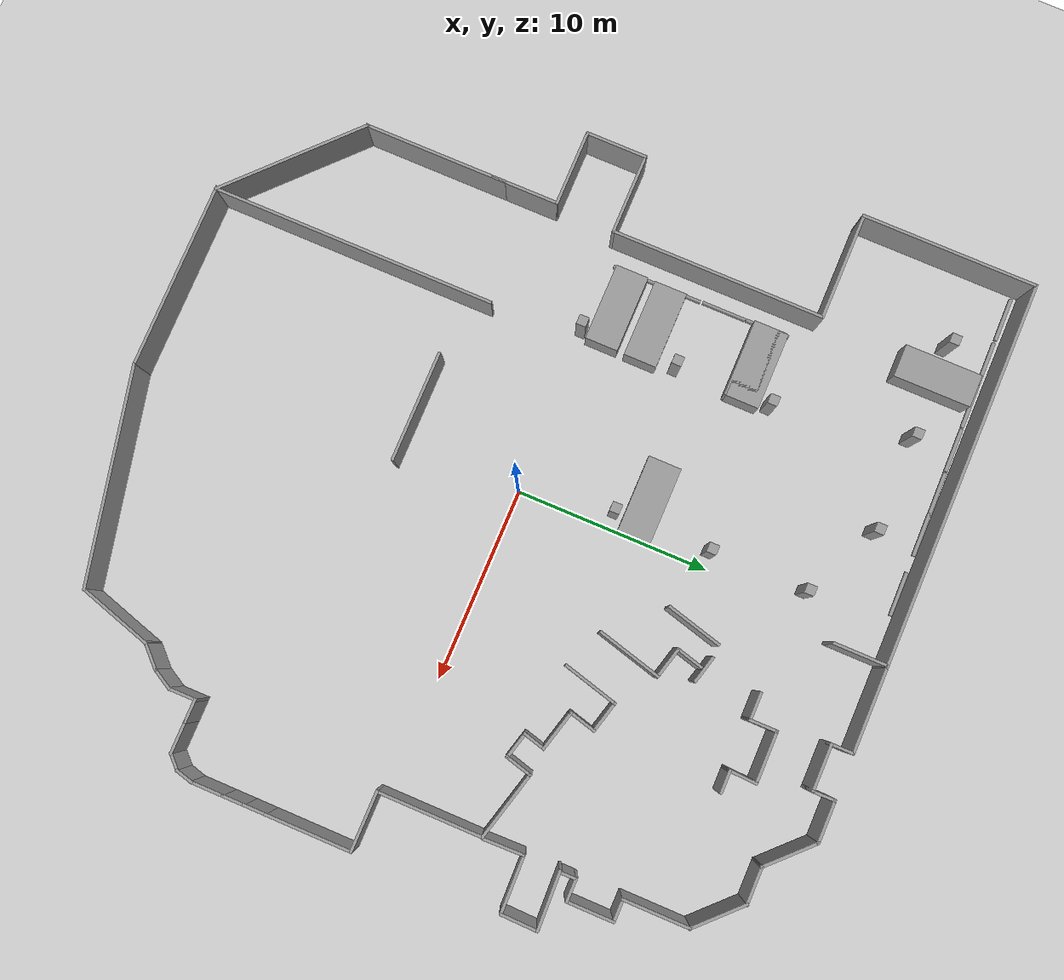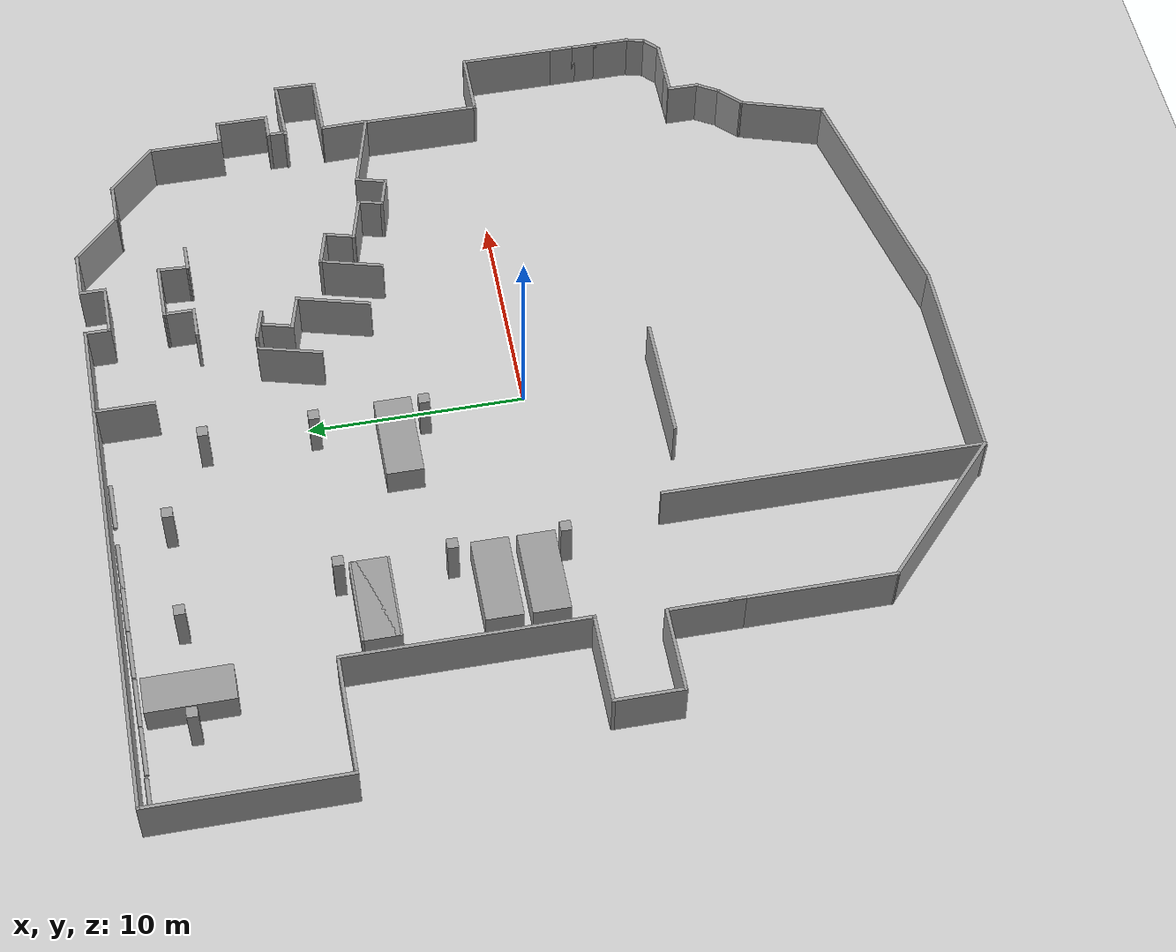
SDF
<sdf version="1.6">
 <world name="default">
  <light name="sun" type="directional">
   <pose>0 0 10 0 -0 0</pose>
   <diffuse>0.8 0.8 0.8 1</diffuse>
   <specular>0.2 0.2 0.2 1</specular>
   <attenuation>
    <range>1000</range>
    <constant>0.9</constant>
    <linear>0.01</linear>
    <quadratic>0.001</quadratic>
   </attenuation>
   <direction>-0.5 0.1 -0.9</direction>
  </light>
  <model name="ground_plane">
   <static>1</static>
   <link name="link">
    <collision name="collision">
     <geometry><plane><normal>0 0 1</normal><size>100 100</size></plane></geometry>
     <surface>
      <contact><collide_bitmask>65535</collide_bitmask></contact>
      <friction><ode><mu>100</mu><mu2>50</mu2></ode></friction>
     </surface>
    </collision>
    <visual name="visual">
     <cast_shadows>0</cast_shadows>
     <geometry><plane><normal>0 0 1</normal><size>100 100</size></plane></geometry>
     <material>
      <script><uri>file://media/materials/scripts/gazebo.material</uri><name>Gazebo/Grey</name></script>
     </material>
    </visual>
   </link>
  </model>
  <gravity>0 0 -9.8</gravity>
  <magnetic_field>6e-06 2.3e-05 -4.2e-05</magnetic_field>
  <atmosphere type="adiabatic"/>
  <physics name="default_physics" default="0" type="ode">
   <max_step_size>0.001</max_step_size>
   <real_time_factor>1</real_time_factor>
   <real_time_update_rate>1000</real_time_update_rate>
   <ode>
    <solver>
     <type>quick</type>
     <iters>200</iters>
     <sor>1.4</sor>
     <use_dynamic_moi_rescaling>0</use_dynamic_moi_rescaling>
    </solver>
    <constraints>
     <cfm>0</cfm>
     <erp>0.2</erp>
     <contact_max_correcting_vel>100</contact_max_correcting_vel>
     <contact_surface_layer>0.001</contact_surface_layer>
    </constraints>
   </ode>
  </physics>
  <scene><ambient>0.4 0.4 0.4 1</ambient><background>0.7 0.7 0.7 1</background><shadows>1</shadows></scene>
  <audio><device>default</device></audio>
  <spherical_coordinates>
   <surface_model>EARTH_WGS84</surface_model>
   <latitude_deg>0</latitude_deg>
   <longitude_deg>0</longitude_deg>
   <elevation>0</elevation>
   <heading_deg>0</heading_deg>
  </spherical_coordinates>
  <model name="walls">
   <pose>-0.02861 -0.0174 0 0 -0 0</pose>
   <link name="Wall_0">
    <collision name="Wall_0_Collision">
     <geometry><box><size>20.15 0.15 2.5</size></box></geometry>
     <pose>0 0 1.25 0 -0 0</pose>
     <surface><contact><collide_bitmask>0x01</collide_bitmask></contact></surface>
    </collision>
    <visual name="Wall_0_Visual">
     <pose>0 0 1.25 0 -0 0</pose>
     <geometry><box><size>20.15 0.15 2.5</size></box></geometry>
     <material>
      <script><uri>file://media/materials/scripts/gazebo.material</uri><name>Gazebo/Grey</name></script>
      <ambient>1 1 1 1</ambient>
     </material>
     <meta><layer>0</layer></meta>
    </visual>
    <pose>-8.81505 19.397 0 0 -0 3.14159</pose>
   </link>
   <link name="Wall_11">
    <collision name="Wall_11_Collision">
     <geometry><box><size>1.25 0.15 2.5</size></box></geometry>
     <pose>0 0 1.25 0 -0 0</pose>
     <surface><contact><collide_bitmask>0x01</collide_bitmask></contact></surface>
    </collision>
    <visual name="Wall_11_Visual">
     <pose>0 0 1.25 0 -0 0</pose>
     <geometry><box><size>1.25 0.15 2.5</size></box></geometry>
     <material>
      <script><uri>file://media/materials/scripts/gazebo.material</uri><name>Gazebo/Grey</name></script>
      <ambient>1 1 1 1</ambient>
     </material>
     <meta><layer>0</layer></meta>
    </visual>
    <pose>5.53495 18.847 0 0 -0 -1.5708</pose>
   </link>
   <link name="Wall_12">
    <collision name="Wall_12_Collision">
     <geometry><box><size>2.5 0.15 2.5</size></box></geometry>
     <pose>0 0 1.25 0 -0 0</pose>
     <surface><contact><collide_bitmask>0x01</collide_bitmask></contact></surface>
    </collision>
    <visual name="Wall_12_Visual">
     <pose>0 0 1.25 0 -0 0</pose>
     <geometry><box><size>2.5 0.15 2.5</size></box></geometry>
     <material>
      <script><uri>file://media/materials/scripts/gazebo.material</uri><name>Gazebo/Grey</name></script>
      <ambient>1 1 1 1</ambient>
     </material>
     <meta><layer>0</layer></meta>
    </visual>
    <pose>6.70995 18.297 0 0 -0 0</pose>
   </link>
   <link name="Wall_13">
    <collision name="Wall_13_Collision">
     <geometry><box><size>1.25 0.15 2.5</size></box></geometry>
     <pose>0 0 1.25 0 -0 0</pose>
     <surface><contact><collide_bitmask>0x01</collide_bitmask></contact></surface>
    </collision>
    <visual name="Wall_13_Visual">
     <pose>0 0 1.25 0 -0 0</pose>
     <geometry><box><size>1.25 0.15 2.5</size></box></geometry>
     <material>
      <script><uri>file://media/materials/scripts/gazebo.material</uri><name>Gazebo/Grey</name></script>
      <ambient>1 1 1 1</ambient>
     </material>
     <meta><layer>0</layer></meta>
    </visual>
    <pose>7.88495 18.847 0 0 -0 1.5708</pose>
   </link>
   <link name="Wall_14">
    <collision name="Wall_14_Collision">
     <geometry><box><size>2.25 0.15 2.5</size></box></geometry>
     <pose>0 0 1.25 0 -0 0</pose>
     <surface><contact><collide_bitmask>0x01</collide_bitmask></contact></surface>
    </collision>
    <visual name="Wall_14_Visual">
     <pose>0 0 1.25 0 -0 0</pose>
     <geometry><box><size>2.25 0.15 2.5</size></box></geometry>
     <material>
      <script><uri>file://media/materials/scripts/gazebo.material</uri><name>Gazebo/Grey</name></script>
      <ambient>1 1 1 1</ambient>
     </material>
     <meta><layer>0</layer></meta>
    </visual>
    <pose>8.93495 19.397 0 0 -0 0</pose>
   </link>
   <link name="Wall_15">
    <collision name="Wall_15_Collision">
     <geometry><box><size>3 0.15 2.5</size></box></geometry>
     <pose>0 0 1.25 0 -0 0</pose>
     <surface><contact><collide_bitmask>0x01</collide_bitmask></contact></surface>
    </collision>
    <visual name="Wall_15_Visual">
     <pose>0 0 1.25 0 -0 0</pose>
     <geometry><box><size>3 0.15 2.5</size></box></geometry>
     <material>
      <script><uri>file://media/materials/scripts/gazebo.material</uri><name>Gazebo/Grey</name></script>
      <ambient>1 1 1 1</ambient>
     </material>
     <meta><layer>0</layer></meta>
    </visual>
    <pose>10.9926 18.3894 0 0 -0 -0.785398</pose>
   </link>
   <link name="Wall_16">
    <collision name="Wall_16_Collision">
     <geometry><box><size>2 0.15 2.5</size></box></geometry>
     <pose>0 0 1.25 0 -0 0</pose>
     <surface><contact><collide_bitmask>0x01</collide_bitmask></contact></surface>
    </collision>
    <visual name="Wall_16_Visual">
     <pose>0 0 1.25 0 -0 0</pose>
     <geometry><box><size>2 0.15 2.5</size></box></geometry>
     <material>
      <script><uri>file://media/materials/scripts/gazebo.material</uri><name>Gazebo/Grey</name></script>
      <ambient>1 1 1 1</ambient>
     </material>
     <meta><layer>0</layer></meta>
    </visual>
    <pose>12.9252 17.3817 0 0 -0 0</pose>
   </link>
   <link name="Wall_18">
    <collision name="Wall_18_Collision">
     <geometry><box><size>3 0.15 2.5</size></box></geometry>
     <pose>0 0 1.25 0 -0 0</pose>
     <surface><contact><collide_bitmask>0x01</collide_bitmask></contact></surface>
    </collision>
    <visual name="Wall_18_Visual">
     <pose>0 0 1.25 0 -0 0</pose>
     <geometry><box><size>3 0.15 2.5</size></box></geometry>
     <material>
      <script><uri>file://media/materials/scripts/gazebo.material</uri><name>Gazebo/Grey</name></script>
      <ambient>1 1 1 1</ambient>
     </material>
     <meta><layer>0</layer></meta>
    </visual>
    <pose>14.8578 16.3741 0 0 -0 -0.785398</pose>
   </link>
   <link name="Wall_19">
    <collision name="Wall_19_Collision">
     <geometry><box><size>3.5 0.15 2.5</size></box></geometry>
     <pose>0 0 1.25 0 -0 0</pose>
     <surface><contact><collide_bitmask>0x01</collide_bitmask></contact></surface>
    </collision>
    <visual name="Wall_19_Visual">
     <pose>0 0 1.25 0 -0 0</pose>
     <geometry><box><size>3.5 0.15 2.5</size></box></geometry>
     <material>
      <script><uri>file://media/materials/scripts/gazebo.material</uri><name>Gazebo/Grey</name></script>
      <ambient>1 1 1 1</ambient>
     </material>
     <meta><layer>0</layer></meta>
    </visual>
    <pose>15.8655 13.6915 0 0 -0 -1.5708</pose>
   </link>
   <link name="Wall_2">
    <collision name="Wall_2_Collision">
     <geometry><box><size>9.15 0.15 2.5</size></box></geometry>
     <pose>0 0 1.25 0 -0 0</pose>
     <surface><contact><collide_bitmask>0x01</collide_bitmask></contact></surface>
    </collision>
    <visual name="Wall_2_Visual">
     <pose>0 0 1.25 0 -0 0</pose>
     <geometry><box><size>9.15 0.15 2.5</size></box></geometry>
     <material>
      <script><uri>file://media/materials/scripts/gazebo.material</uri><name>Gazebo/Grey</name></script>
      <ambient>1 1 1 1</ambient>
     </material>
     <meta><layer>0</layer></meta>
    </visual>
    <pose>-18.8151 14.897 0 0 -0 -1.5708</pose>
   </link>
   <link name="Wall_20">
    <collision name="Wall_20_Collision">
     <geometry><box><size>1.25 0.15 2.5</size></box></geometry>
     <pose>0 0 1.25 0 -0 0</pose>
     <surface><contact><collide_bitmask>0x01</collide_bitmask></contact></surface>
    </collision>
    <visual name="Wall_20_Visual">
     <pose>0 0 1.25 0 -0 0</pose>
     <geometry><box><size>1.25 0.15 2.5</size></box></geometry>
     <material>
      <script><uri>file://media/materials/scripts/gazebo.material</uri><name>Gazebo/Grey</name></script>
      <ambient>1 1 1 1</ambient>
     </material>
     <meta><layer>0</layer></meta>
    </visual>
    <pose>16.4157 12.0162 0 0 -0 -0.000446</pose>
   </link>
   <link name="Wall_21">
    <collision name="Wall_21_Collision">
     <geometry><box><size>2.5 0.15 2.5</size></box></geometry>
     <pose>0 0 1.25 0 -0 0</pose>
     <surface><contact><collide_bitmask>0x01</collide_bitmask></contact></surface>
    </collision>
    <visual name="Wall_21_Visual">
     <pose>0 0 1.25 0 -0 0</pose>
     <geometry><box><size>2.5 0.15 2.5</size></box></geometry>
     <material>
      <script><uri>file://media/materials/scripts/gazebo.material</uri><name>Gazebo/Grey</name></script>
      <ambient>1 1 1 1</ambient>
     </material>
     <meta><layer>0</layer></meta>
    </visual>
    <pose>16.9659 10.841 0 0 -0 -1.5708</pose>
   </link>
   <link name="Wall_22">
    <collision name="Wall_22_Collision">
     <geometry><box><size>1.25 0.15 2.5</size></box></geometry>
     <pose>0 0 1.25 0 -0 0</pose>
     <surface><contact><collide_bitmask>0x01</collide_bitmask></contact></surface>
    </collision>
    <visual name="Wall_22_Visual">
     <pose>0 0 1.25 0 -0 0</pose>
     <geometry><box><size>1.25 0.15 2.5</size></box></geometry>
     <material>
      <script><uri>file://media/materials/scripts/gazebo.material</uri><name>Gazebo/Grey</name></script>
      <ambient>1 1 1 1</ambient>
     </material>
     <meta><layer>0</layer></meta>
    </visual>
    <pose>16.4159 9.66599 0 0 -0 3.14159</pose>
   </link>
   <link name="Wall_23">
    <collision name="Wall_23_Collision">
     <geometry><box><size>0.924056 0.15 2.5</size></box></geometry>
     <pose>0 0 1.25 0 -0 0</pose>
     <surface><contact><collide_bitmask>0x01</collide_bitmask></contact></surface>
    </collision>
    <visual name="Wall_23_Visual">
     <pose>0 0 1.25 0 -0 0</pose>
     <geometry><box><size>0.924056 0.15 2.5</size></box></geometry>
     <material>
      <script><uri>file://media/materials/scripts/gazebo.material</uri><name>Gazebo/Grey</name></script>
      <ambient>1 1 1 1</ambient>
     </material>
     <meta><layer>0</layer></meta>
    </visual>
    <pose>15.8657 9.27896 0 0 -0 -1.57143</pose>
   </link>
   <link name="Wall_24">
    <collision name="Wall_24_Collision">
     <geometry><box><size>3.04637 0.15 2.5</size></box></geometry>
     <pose>0 0 1.25 0 -0 0</pose>
     <surface><contact><collide_bitmask>0x01</collide_bitmask></contact></surface>
    </collision>
    <visual name="Wall_24_Visual">
     <pose>0 0 1.25 0 -0 0</pose>
     <geometry><box><size>3.04637 0.15 2.5</size></box></geometry>
     <material>
      <script><uri>file://media/materials/scripts/gazebo.material</uri><name>Gazebo/Grey</name></script>
      <ambient>1 1 1 1</ambient>
     </material>
     <meta><layer>0</layer></meta>
    </visual>
    <pose>17.268 8.89193 0 0 -0 0.031058</pose>
   </link>
   <link name="Wall_25">
    <collision name="Wall_25_Collision">
     <geometry><box><size>2 0.15 2.5</size></box></geometry>
     <pose>0 0 1.25 0 -0 0</pose>
     <surface><contact><collide_bitmask>0x01</collide_bitmask></contact></surface>
    </collision>
    <visual name="Wall_25_Visual">
     <pose>0 0 1.25 0 -0 0</pose>
     <geometry><box><size>2 0.15 2.5</size></box></geometry>
     <material>
      <script><uri>file://media/materials/scripts/gazebo.material</uri><name>Gazebo/Grey</name></script>
      <ambient>1 1 1 1</ambient>
     </material>
     <meta><layer>0</layer></meta>
    </visual>
    <pose>18.6977 8.01207 0 0 -0 -1.58997</pose>
   </link>
   <link name="Wall_26">
    <collision name="Wall_26_Collision">
     <geometry><box><size>3.01012 0.15 2.5</size></box></geometry>
     <pose>0 0 1.25 0 -0 0</pose>
     <surface><contact><collide_bitmask>0x01</collide_bitmask></contact></surface>
    </collision>
    <visual name="Wall_26_Visual">
     <pose>0 0 1.25 0 -0 0</pose>
     <geometry><box><size>3.01012 0.15 2.5</size></box></geometry>
     <material>
      <script><uri>file://media/materials/scripts/gazebo.material</uri><name>Gazebo/Grey</name></script>
      <ambient>1 1 1 1</ambient>
     </material>
     <meta><layer>0</layer></meta>
    </visual>
    <pose>17.2502 7.05734 0 0 -0 -3.12068</pose>
   </link>
   <link name="Wall_27">
    <collision name="Wall_27_Collision">
     <geometry><box><size>2.15523 0.15 2.5</size></box></geometry>
     <pose>0 0 1.25 0 -0 0</pose>
     <surface><contact><collide_bitmask>0x01</collide_bitmask></contact></surface>
    </collision>
    <visual name="Wall_27_Visual">
     <pose>0 0 1.25 0 -0 0</pose>
     <geometry><box><size>2.15523 0.15 2.5</size></box></geometry>
     <material>
      <script><uri>file://media/materials/scripts/gazebo.material</uri><name>Gazebo/Grey</name></script>
      <ambient>1 1 1 1</ambient>
     </material>
     <meta><layer>0</layer></meta>
    </visual>
    <pose>15.843 5.98011 0 0 -0 -1.54837</pose>
   </link>
   <link name="Wall_28">
    <collision name="Wall_28_Collision">
     <geometry><box><size>3.75 0.15 2.5</size></box></geometry>
     <pose>0 0 1.25 0 -0 0</pose>
     <surface><contact><collide_bitmask>0x01</collide_bitmask></contact></surface>
    </collision>
    <visual name="Wall_28_Visual">
     <pose>0 0 1.25 0 -0 0</pose>
     <geometry><box><size>3.75 0.15 2.5</size></box></geometry>
     <material>
      <script><uri>file://media/materials/scripts/gazebo.material</uri><name>Gazebo/Grey</name></script>
      <ambient>1 1 1 1</ambient>
     </material>
     <meta><layer>0</layer></meta>
    </visual>
    <pose>14.0818 5.39865 0 0 -0 2.87979</pose>
   </link>
   <link name="Wall_32">
    <collision name="Wall_32_Collision">
     <geometry><box><size>2.75 0.15 2.5</size></box></geometry>
     <pose>0 0 1.25 0 -0 0</pose>
     <surface><contact><collide_bitmask>0x01</collide_bitmask></contact></surface>
    </collision>
    <visual name="Wall_32_Visual">
     <pose>0 0 1.25 0 -0 0</pose>
     <geometry><box><size>2.75 0.15 2.5</size></box></geometry>
     <material>
      <script><uri>file://media/materials/scripts/gazebo.material</uri><name>Gazebo/Grey</name></script>
      <ambient>1 1 1 1</ambient>
     </material>
     <meta><layer>0</layer></meta>
    </visual>
    <pose>1.11456 18.0056 0 0 -0 -1.5708</pose>
   </link>
   <link name="Wall_34">
    <collision name="Wall_34_Collision">
     <geometry><box><size>1.5 0.15 2.5</size></box></geometry>
     <pose>0 0 1.25 0 -0 0</pose>
     <surface><contact><collide_bitmask>0x01</collide_bitmask></contact></surface>
    </collision>
    <visual name="Wall_34_Visual">
     <pose>0 0 1.25 0 -0 0</pose>
     <geometry><box><size>1.5 0.15 2.5</size></box></geometry>
     <material>
      <script><uri>file://media/materials/scripts/gazebo.material</uri><name>Gazebo/Grey</name></script>
      <ambient>1 1 1 1</ambient>
     </material>
     <meta><layer>0</layer></meta>
    </visual>
    <pose>12.1684 5.21253 0 0 -0 -1.8326</pose>
   </link>
   <link name="Wall_35">
    <collision name="Wall_35_Collision">
     <geometry><box><size>1.5 0.15 2.5</size></box></geometry>
     <pose>0 0 1.25 0 -0 0</pose>
     <surface><contact><collide_bitmask>0x01</collide_bitmask></contact></surface>
    </collision>
    <visual name="Wall_35_Visual">
     <pose>0 0 1.25 0 -0 0</pose>
     <geometry><box><size>1.5 0.15 2.5</size></box></geometry>
     <material>
      <script><uri>file://media/materials/scripts/gazebo.material</uri><name>Gazebo/Grey</name></script>
      <ambient>1 1 1 1</ambient>
     </material>
     <meta><layer>0</layer></meta>
    </visual>
    <pose>11.3417 4.73523 0 0 -0 2.87979</pose>
   </link>
   <link name="Wall_36">
    <collision name="Wall_36_Collision">
     <geometry><box><size>1.25 0.15 2.5</size></box></geometry>
     <pose>0 0 1.25 0 -0 0</pose>
     <surface><contact><collide_bitmask>0x01</collide_bitmask></contact></surface>
    </collision>
    <visual name="Wall_36_Visual">
     <pose>0 0 1.25 0 -0 0</pose>
     <geometry><box><size>1.25 0.15 2.5</size></box></geometry>
     <material>
      <script><uri>file://media/materials/scripts/gazebo.material</uri><name>Gazebo/Grey</name></script>
      <ambient>1 1 1 1</ambient>
     </material>
     <meta><layer>0</layer></meta>
    </visual>
    <pose>10.8321 5.44119 0 0 -0 1.309</pose>
   </link>
   <link name="Wall_37">
    <collision name="Wall_37_Collision">
     <geometry><box><size>2.25 0.15 2.5</size></box></geometry>
     <pose>0 0 1.25 0 -0 0</pose>
     <surface><contact><collide_bitmask>0x01</collide_bitmask></contact></surface>
    </collision>
    <visual name="Wall_37_Visual">
     <pose>0 0 1.25 0 -0 0</pose>
     <geometry><box><size>2.25 0.15 2.5</size></box></geometry>
     <material>
      <script><uri>file://media/materials/scripts/gazebo.material</uri><name>Gazebo/Grey</name></script>
      <ambient>1 1 1 1</ambient>
     </material>
     <meta><layer>0</layer></meta>
    </visual>
    <pose>9.96022 6.24421 0 0 -0 2.87979</pose>
   </link>
   <link name="Wall_38">
    <collision name="Wall_38_Collision">
     <geometry><box><size>1.5 0.15 2.5</size></box></geometry>
     <pose>0 0 1.25 0 -0 0</pose>
     <surface><contact><collide_bitmask>0x01</collide_bitmask></contact></surface>
    </collision>
    <visual name="Wall_38_Visual">
     <pose>0 0 1.25 0 -0 0</pose>
     <geometry><box><size>1.5 0.15 2.5</size></box></geometry>
     <material>
      <script><uri>file://media/materials/scripts/gazebo.material</uri><name>Gazebo/Grey</name></script>
      <ambient>1 1 1 1</ambient>
     </material>
     <meta><layer>0</layer></meta>
    </visual>
    <pose>9.12071 7.16797 0 0 -0 1.309</pose>
   </link>
   <link name="Wall_39">
    <collision name="Wall_39_Collision">
     <geometry><box><size>1.75 0.15 2.5</size></box></geometry>
     <pose>0 0 1.25 0 -0 0</pose>
     <surface><contact><collide_bitmask>0x01</collide_bitmask></contact></surface>
    </collision>
    <visual name="Wall_39_Visual">
     <pose>0 0 1.25 0 -0 0</pose>
     <geometry><box><size>1.75 0.15 2.5</size></box></geometry>
     <material>
      <script><uri>file://media/materials/scripts/gazebo.material</uri><name>Gazebo/Grey</name></script>
      <ambient>1 1 1 1</ambient>
     </material>
     <meta><layer>0</layer></meta>
    </visual>
    <pose>8.52267 8.02702 0 0 -0 2.87979</pose>
   </link>
   <link name="Wall_4">
    <collision name="Wall_4_Collision">
     <geometry><box><size>5.65 0.15 2.5</size></box></geometry>
     <pose>0 0 1.25 0 -0 0</pose>
     <surface><contact><collide_bitmask>0x01</collide_bitmask></contact></surface>
    </collision>
    <visual name="Wall_4_Visual">
     <pose>0 0 1.25 0 -0 0</pose>
     <geometry><box><size>5.65 0.15 2.5</size></box></geometry>
     <material>
      <script><uri>file://media/materials/scripts/gazebo.material</uri><name>Gazebo/Grey</name></script>
      <ambient>1 1 1 1</ambient>
     </material>
     <meta><layer>0</layer></meta>
    </visual>
    <pose>-16.0651 10.397 0 0 -0 0</pose>
   </link>
   <link name="Wall_40">
    <collision name="Wall_40_Collision">
     <geometry><box><size>3 0.15 2.5</size></box></geometry>
     <pose>0 0 1.25 0 -0 0</pose>
     <surface><contact><collide_bitmask>0x01</collide_bitmask></contact></surface>
    </collision>
    <visual name="Wall_40_Visual">
     <pose>0 0 1.25 0 -0 0</pose>
     <geometry><box><size>3 0.15 2.5</size></box></geometry>
     <material>
      <script><uri>file://media/materials/scripts/gazebo.material</uri><name>Gazebo/Grey</name></script>
      <ambient>1 1 1 1</ambient>
     </material>
     <meta><layer>0</layer></meta>
    </visual>
    <pose>7.38111 6.85764 0 0 -0 -1.8326</pose>
   </link>
   <link name="Wall_42">
    <collision name="Wall_42_Collision">
     <geometry><box><size>3.5 0.15 2.5</size></box></geometry>
     <pose>0 0 1.25 0 -0 0</pose>
     <surface><contact><collide_bitmask>0x01</collide_bitmask></contact></surface>
    </collision>
    <visual name="Wall_42_Visual">
     <pose>0 0 1.25 0 -0 0</pose>
     <geometry><box><size>3.5 0.15 2.5</size></box></geometry>
     <material>
      <script><uri>file://media/materials/scripts/gazebo.material</uri><name>Gazebo/Grey</name></script>
      <ambient>1 1 1 1</ambient>
     </material>
     <meta><layer>0</layer></meta>
    </visual>
    <pose>5.36205 7.99712 0 0 -0 1.309</pose>
   </link>
   <link name="Wall_43">
    <collision name="Wall_43_Collision">
     <geometry><box><size>1.75 0.15 2.5</size></box></geometry>
     <pose>0 0 1.25 0 -0 0</pose>
     <surface><contact><collide_bitmask>0x01</collide_bitmask></contact></surface>
    </collision>
    <visual name="Wall_43_Visual">
     <pose>0 0 1.25 0 -0 0</pose>
     <geometry><box><size>1.75 0.15 2.5</size></box></geometry>
     <material>
      <script><uri>file://media/materials/scripts/gazebo.material</uri><name>Gazebo/Grey</name></script>
      <ambient>1 1 1 1</ambient>
     </material>
     <meta><layer>0</layer></meta>
    </visual>
    <pose>5.02283 9.8221 0 0 -0 2.87979</pose>
   </link>
   <link name="Wall_44">
    <collision name="Wall_44_Collision">
     <geometry><box><size>1.5 0.15 2.5</size></box></geometry>
     <pose>0 0 1.25 0 -0 0</pose>
     <surface><contact><collide_bitmask>0x01</collide_bitmask></contact></surface>
    </collision>
    <visual name="Wall_44_Visual">
     <pose>0 0 1.25 0 -0 0</pose>
     <geometry><box><size>1.5 0.15 2.5</size></box></geometry>
     <material>
      <script><uri>file://media/materials/scripts/gazebo.material</uri><name>Gazebo/Grey</name></script>
      <ambient>1 1 1 1</ambient>
     </material>
     <meta><layer>0</layer></meta>
    </visual>
    <pose>4.42479 10.6812 0 0 -0 1.309</pose>
   </link>
   <link name="Wall_45">
    <collision name="Wall_45_Collision">
     <geometry><box><size>1.5 0.15 2.5</size></box></geometry>
     <pose>0 0 1.25 0 -0 0</pose>
     <surface><contact><collide_bitmask>0x01</collide_bitmask></contact></surface>
    </collision>
    <visual name="Wall_45_Visual">
     <pose>0 0 1.25 0 -0 0</pose>
     <geometry><box><size>1.5 0.15 2.5</size></box></geometry>
     <material>
      <script><uri>file://media/materials/scripts/gazebo.material</uri><name>Gazebo/Grey</name></script>
      <ambient>1 1 1 1</ambient>
     </material>
     <meta><layer>0</layer></meta>
    </visual>
    <pose>4.64749 11.5079 0 0 -0 2.87979</pose>
   </link>
   <link name="Wall_46">
    <collision name="Wall_46_Collision">
     <geometry><box><size>3 0.15 2.5</size></box></geometry>
     <pose>0 0 1.25 0 -0 0</pose>
     <surface><contact><collide_bitmask>0x01</collide_bitmask></contact></surface>
    </collision>
    <visual name="Wall_46_Visual">
     <pose>0 0 1.25 0 -0 0</pose>
     <geometry><box><size>3 0.15 2.5</size></box></geometry>
     <material>
      <script><uri>file://media/materials/scripts/gazebo.material</uri><name>Gazebo/Grey</name></script>
      <ambient>1 1 1 1</ambient>
     </material>
     <meta><layer>0</layer></meta>
    </visual>
    <pose>2.92668 10.3061 0 0 -0 -1.8326</pose>
   </link>
   <link name="Wall_49">
    <collision name="Wall_49_Collision">
     <geometry><box><size>5.5 0.15 2.5</size></box></geometry>
     <pose>0 0 1.25 0 -0 0</pose>
     <surface><contact><collide_bitmask>0x01</collide_bitmask></contact></surface>
    </collision>
    <visual name="Wall_49_Visual">
     <pose>0 0 1.25 0 -0 0</pose>
     <geometry><box><size>5.5 0.15 2.5</size></box></geometry>
     <material>
      <script><uri>file://media/materials/scripts/gazebo.material</uri><name>Gazebo/Grey</name></script>
      <ambient>1 1 1 1</ambient>
     </material>
     <meta><layer>0</layer></meta>
    </visual>
    <pose>15.8205 2.25778 0 0 -0 -1.5708</pose>
   </link>
   <link name="Wall_51">
    <collision name="Wall_51_Collision">
     <geometry><box><size>4.25 0.15 2.5</size></box></geometry>
     <pose>0 0 1.25 0 -0 0</pose>
     <surface><contact><collide_bitmask>0x01</collide_bitmask></contact></surface>
    </collision>
    <visual name="Wall_51_Visual">
     <pose>0 0 1.25 0 -0 0</pose>
     <geometry><box><size>4.25 0.15 2.5</size></box></geometry>
     <material>
      <script><uri>file://media/materials/scripts/gazebo.material</uri><name>Gazebo/Grey</name></script>
      <ambient>1 1 1 1</ambient>
     </material>
     <meta><layer>0</layer></meta>
    </visual>
    <pose>-15.3651 -0.603013 0 0 -0 3.14159</pose>
   </link>
   <link name="Wall_52">
    <collision name="Wall_52_Collision">
     <geometry><box><size>3.25 0.15 2.5</size></box></geometry>
     <pose>0 0 1.25 0 -0 0</pose>
     <surface><contact><collide_bitmask>0x01</collide_bitmask></contact></surface>
    </collision>
    <visual name="Wall_52_Visual">
     <pose>0 0 1.25 0 -0 0</pose>
     <geometry><box><size>3.25 0.15 2.5</size></box></geometry>
     <material>
      <script><uri>file://media/materials/scripts/gazebo.material</uri><name>Gazebo/Grey</name></script>
      <ambient>1 1 1 1</ambient>
     </material>
     <meta><layer>0</layer></meta>
    </visual>
    <pose>-17.4151 -2.15301 0 0 -0 -1.5708</pose>
   </link>
   <link name="Wall_53">
    <collision name="Wall_53_Collision">
     <geometry><box><size>4 0.15 2.5</size></box></geometry>
     <pose>0 0 1.25 0 -0 0</pose>
     <surface><contact><collide_bitmask>0x01</collide_bitmask></contact></surface>
    </collision>
    <visual name="Wall_53_Visual">
     <pose>0 0 1.25 0 -0 0</pose>
     <geometry><box><size>4 0.15 2.5</size></box></geometry>
     <material>
      <script><uri>file://media/materials/scripts/gazebo.material</uri><name>Gazebo/Grey</name></script>
      <ambient>1 1 1 1</ambient>
     </material>
     <meta><layer>0</layer></meta>
    </visual>
    <pose>-15.4901 -3.70301 0 0 -0 0</pose>
   </link>
   <link name="Wall_55">
    <collision name="Wall_55_Collision">
     <geometry><box><size>3.5 0.15 2.5</size></box></geometry>
     <pose>0 0 1.25 0 -0 0</pose>
     <surface><contact><collide_bitmask>0x01</collide_bitmask></contact></surface>
    </collision>
    <visual name="Wall_55_Visual">
     <pose>0 0 1.25 0 -0 0</pose>
     <geometry><box><size>3.5 0.15 2.5</size></box></geometry>
     <material>
      <script><uri>file://media/materials/scripts/gazebo.material</uri><name>Gazebo/Grey</name></script>
      <ambient>1 1 1 1</ambient>
     </material>
     <meta><layer>0</layer></meta>
    </visual>
    <pose>-13.5474 -5.43216 0 0 -0 -1.5708</pose>
   </link>
   <link name="Wall_56">
    <collision name="Wall_56_Collision">
     <geometry><box><size>7.5 0.15 2.5</size></box></geometry>
     <pose>0 0 1.25 0 -0 0</pose>
     <surface><contact><collide_bitmask>0x01</collide_bitmask></contact></surface>
    </collision>
    <visual name="Wall_56_Visual">
     <pose>0 0 1.25 0 -0 0</pose>
     <geometry><box><size>7.5 0.15 2.5</size></box></geometry>
     <material>
      <script><uri>file://media/materials/scripts/gazebo.material</uri><name>Gazebo/Grey</name></script>
      <ambient>1 1 1 1</ambient>
     </material>
     <meta><layer>0</layer></meta>
    </visual>
    <pose>-13.5474 -10.1822 0 0 -0 -1.5708</pose>
   </link>
   <link name="Wall_57">
    <collision name="Wall_57_Collision">
     <geometry><box><size>8.20684 0.15 2.5</size></box></geometry>
     <pose>0 0 1.25 0 -0 0</pose>
     <surface><contact><collide_bitmask>0x01</collide_bitmask></contact></surface>
    </collision>
    <visual name="Wall_57_Visual">
     <pose>0 0 1.25 0 -0 0</pose>
     <geometry><box><size>8.20684 0.15 2.5</size></box></geometry>
     <material>
      <script><uri>file://media/materials/scripts/gazebo.material</uri><name>Gazebo/Grey</name></script>
      <ambient>1 1 1 1</ambient>
     </material>
     <meta><layer>0</layer></meta>
    </visual>
    <pose>-10.6224 -16.6271 0 0 -0 -0.758176</pose>
   </link>
   <link name="Wall_58">
    <collision name="Wall_58_Collision">
     <geometry><box><size>14.7899 0.15 2.5</size></box></geometry>
     <pose>0 0 1.25 0 -0 0</pose>
     <surface><contact><collide_bitmask>0x01</collide_bitmask></contact></surface>
    </collision>
    <visual name="Wall_58_Visual">
     <pose>0 0 1.25 0 -0 0</pose>
     <geometry><box><size>14.7899 0.15 2.5</size></box></geometry>
     <material>
      <script><uri>file://media/materials/scripts/gazebo.material</uri><name>Gazebo/Grey</name></script>
      <ambient>1 1 1 1</ambient>
     </material>
     <meta><layer>0</layer></meta>
    </visual>
    <pose>-7.69736 -12.0771 0 0 -0 1.5708</pose>
   </link>
   <link name="Wall_6">
    <collision name="Wall_6_Collision">
     <geometry><box><size>11.15 0.15 2.5</size></box></geometry>
     <pose>0 0 1.25 0 -0 0</pose>
     <surface><contact><collide_bitmask>0x01</collide_bitmask></contact></surface>
    </collision>
    <visual name="Wall_6_Visual">
     <pose>0 0 1.25 0 -0 0</pose>
     <geometry><box><size>11.15 0.15 2.5</size></box></geometry>
     <material>
      <script><uri>file://media/materials/scripts/gazebo.material</uri><name>Gazebo/Grey</name></script>
      <ambient>1 1 1 1</ambient>
     </material>
     <meta><layer>0</layer></meta>
    </visual>
    <pose>-13.3151 4.89699 0 0 -0 -1.5708</pose>
   </link>
   <link name="Wall_60">
    <collision name="Wall_60_Collision">
     <geometry><box><size>5.75 0.15 2.5</size></box></geometry>
     <pose>0 0 1.25 0 -0 0</pose>
     <surface><contact><collide_bitmask>0x01</collide_bitmask></contact></surface>
    </collision>
    <visual name="Wall_60_Visual">
     <pose>0 0 1.25 0 -0 0</pose>
     <geometry><box><size>5.75 0.15 2.5</size></box></geometry>
     <material>
      <script><uri>file://media/materials/scripts/gazebo.material</uri><name>Gazebo/Grey</name></script>
      <ambient>1 1 1 1</ambient>
     </material>
     <meta><layer>0</layer></meta>
    </visual>
    <pose>-1.597 -6.03066 0 0 -0 0</pose>
   </link>
   <link name="Wall_62">
    <collision name="Wall_62_Collision">
     <geometry><box><size>9.75 0.15 2.5</size></box></geometry>
     <pose>0 0 1.25 0 -0 0</pose>
     <surface><contact><collide_bitmask>0x01</collide_bitmask></contact></surface>
    </collision>
    <visual name="Wall_62_Visual">
     <pose>0 0 1.25 0 -0 0</pose>
     <geometry><box><size>9.75 0.15 2.5</size></box></geometry>
     <material>
      <script><uri>file://media/materials/scripts/gazebo.material</uri><name>Gazebo/Grey</name></script>
      <ambient>1 1 1 1</ambient>
     </material>
     <meta><layer>0</layer></meta>
    </visual>
    <pose>-2.96575 -19.397 0 0 -0 0</pose>
   </link>
   <link name="Wall_64">
    <collision name="Wall_64_Collision">
     <geometry><box><size>11.191 0.15 2.5</size></box></geometry>
     <pose>0 0 1.25 0 -0 0</pose>
     <surface><contact><collide_bitmask>0x01</collide_bitmask></contact></surface>
    </collision>
    <visual name="Wall_64_Visual">
     <pose>0 0 1.25 0 -0 0</pose>
     <geometry><box><size>11.191 0.15 2.5</size></box></geometry>
     <material>
      <script><uri>file://media/materials/scripts/gazebo.material</uri><name>Gazebo/Grey</name></script>
      <ambient>1 1 1 1</ambient>
     </material>
     <meta><layer>0</layer></meta>
    </visual>
    <pose>7.22297 -18.1981 0 0 -0 0.21892</pose>
   </link>
   <link name="Wall_65">
    <collision name="Wall_65_Collision">
     <geometry><box><size>4.07583 0.15 2.5</size></box></geometry>
     <pose>0 0 1.25 0 -0 0</pose>
     <surface><contact><collide_bitmask>0x01</collide_bitmask></contact></surface>
    </collision>
    <visual name="Wall_65_Visual">
     <pose>0 0 1.25 0 -0 0</pose>
     <geometry><box><size>4.07583 0.15 2.5</size></box></geometry>
     <material>
      <script><uri>file://media/materials/scripts/gazebo.material</uri><name>Gazebo/Grey</name></script>
      <ambient>1 1 1 1</ambient>
     </material>
     <meta><layer>0</layer></meta>
    </visual>
    <pose>13.1921 -15.1241 0 0 -0 1.27061</pose>
   </link>
   <link name="Wall_66">
    <collision name="Wall_66_Collision">
     <geometry><box><size>1.5 0.15 2.5</size></box></geometry>
     <pose>0 0 1.25 0 -0 0</pose>
     <surface><contact><collide_bitmask>0x01</collide_bitmask></contact></surface>
    </collision>
    <visual name="Wall_66_Visual">
     <pose>0 0 1.25 0 -0 0</pose>
     <geometry><box><size>1.5 0.15 2.5</size></box></geometry>
     <material>
      <script><uri>file://media/materials/scripts/gazebo.material</uri><name>Gazebo/Grey</name></script>
      <ambient>1 1 1 1</ambient>
     </material>
     <meta><layer>0</layer></meta>
    </visual>
    <pose>14.2499 -12.7716 0 0 -0 0.785398</pose>
   </link>
   <link name="Wall_67">
    <collision name="Wall_67_Collision">
     <geometry><box><size>1.25 0.15 2.5</size></box></geometry>
     <pose>0 0 1.25 0 -0 0</pose>
     <surface><contact><collide_bitmask>0x01</collide_bitmask></contact></surface>
    </collision>
    <visual name="Wall_67_Visual">
     <pose>0 0 1.25 0 -0 0</pose>
     <geometry><box><size>1.25 0.15 2.5</size></box></geometry>
     <material>
      <script><uri>file://media/materials/scripts/gazebo.material</uri><name>Gazebo/Grey</name></script>
      <ambient>1 1 1 1</ambient>
     </material>
     <meta><layer>0</layer></meta>
    </visual>
    <pose>15.0022 -11.818 0 0 -0 1.0472</pose>
   </link>
   <link name="Wall_68">
    <collision name="Wall_68_Collision">
     <geometry><box><size>1.5 0.15 2.5</size></box></geometry>
     <pose>0 0 1.25 0 -0 0</pose>
     <surface><contact><collide_bitmask>0x01</collide_bitmask></contact></surface>
    </collision>
    <visual name="Wall_68_Visual">
     <pose>0 0 1.25 0 -0 0</pose>
     <geometry><box><size>1.5 0.15 2.5</size></box></geometry>
     <material>
      <script><uri>file://media/materials/scripts/gazebo.material</uri><name>Gazebo/Grey</name></script>
      <ambient>1 1 1 1</ambient>
     </material>
     <meta><layer>0</layer></meta>
    </visual>
    <pose>15.2772 -10.6667 0 0 -0 1.5708</pose>
   </link>
   <link name="Wall_69">
    <collision name="Wall_69_Collision">
     <geometry><box><size>1.25 0.15 2.5</size></box></geometry>
     <pose>0 0 1.25 0 -0 0</pose>
     <surface><contact><collide_bitmask>0x01</collide_bitmask></contact></surface>
    </collision>
    <visual name="Wall_69_Visual">
     <pose>0 0 1.25 0 -0 0</pose>
     <geometry><box><size>1.25 0.15 2.5</size></box></geometry>
     <material>
      <script><uri>file://media/materials/scripts/gazebo.material</uri><name>Gazebo/Grey</name></script>
      <ambient>1 1 1 1</ambient>
     </material>
     <meta><layer>0</layer></meta>
    </visual>
    <pose>15.8272 -9.99171 0 0 -0 0</pose>
   </link>
   <link name="Wall_70">
    <collision name="Wall_70_Collision">
     <geometry><box><size>1.75 0.15 2.5</size></box></geometry>
     <pose>0 0 1.25 0 -0 0</pose>
     <surface><contact><collide_bitmask>0x01</collide_bitmask></contact></surface>
    </collision>
    <visual name="Wall_70_Visual">
     <pose>0 0 1.25 0 -0 0</pose>
     <geometry><box><size>1.75 0.15 2.5</size></box></geometry>
     <material>
      <script><uri>file://media/materials/scripts/gazebo.material</uri><name>Gazebo/Grey</name></script>
      <ambient>1 1 1 1</ambient>
     </material>
     <meta><layer>0</layer></meta>
    </visual>
    <pose>17.1772 -9.99171 0 0 -0 0</pose>
   </link>
   <link name="Wall_71">
    <collision name="Wall_71_Collision">
     <geometry><box><size>1 0.15 2.5</size></box></geometry>
     <pose>0 0 1.25 0 -0 0</pose>
     <surface><contact><collide_bitmask>0x01</collide_bitmask></contact></surface>
    </collision>
    <visual name="Wall_71_Visual">
     <pose>0 0 1.25 0 -0 0</pose>
     <geometry><box><size>1 0.15 2.5</size></box></geometry>
     <material>
      <script><uri>file://media/materials/scripts/gazebo.material</uri><name>Gazebo/Grey</name></script>
      <ambient>1 1 1 1</ambient>
     </material>
     <meta><layer>0</layer></meta>
    </visual>
    <pose>18.2777 -9.69119 0 0 -0 0.785398</pose>
   </link>
   <link name="Wall_72">
    <collision name="Wall_72_Collision">
     <geometry><box><size>1 0.15 2.5</size></box></geometry>
     <pose>0 0 1.25 0 -0 0</pose>
     <surface><contact><collide_bitmask>0x01</collide_bitmask></contact></surface>
    </collision>
    <visual name="Wall_72_Visual">
     <pose>0 0 1.25 0 -0 0</pose>
     <geometry><box><size>1 0.15 2.5</size></box></geometry>
     <material>
      <script><uri>file://media/materials/scripts/gazebo.material</uri><name>Gazebo/Grey</name></script>
      <ambient>1 1 1 1</ambient>
     </material>
     <meta><layer>0</layer></meta>
    </visual>
    <pose>18.6882 -8.98015 0 0 -0 1.309</pose>
   </link>
   <link name="Wall_73">
    <collision name="Wall_73_Collision">
     <geometry><box><size>1.75 0.15 2.5</size></box></geometry>
     <pose>0 0 1.25 0 -0 0</pose>
     <surface><contact><collide_bitmask>0x01</collide_bitmask></contact></surface>
    </collision>
    <visual name="Wall_73_Visual">
     <pose>0 0 1.25 0 -0 0</pose>
     <geometry><box><size>1.75 0.15 2.5</size></box></geometry>
     <material>
      <script><uri>file://media/materials/scripts/gazebo.material</uri><name>Gazebo/Grey</name></script>
      <ambient>1 1 1 1</ambient>
     </material>
     <meta><layer>0</layer></meta>
    </visual>
    <pose>18.7982 -7.76963 0 0 -0 1.5708</pose>
   </link>
   <link name="Wall_74">
    <collision name="Wall_74_Collision">
     <geometry><box><size>1.25 0.15 2.5</size></box></geometry>
     <pose>0 0 1.25 0 -0 0</pose>
     <surface><contact><collide_bitmask>0x01</collide_bitmask></contact></surface>
    </collision>
    <visual name="Wall_74_Visual">
     <pose>0 0 1.25 0 -0 0</pose>
     <geometry><box><size>1.25 0.15 2.5</size></box></geometry>
     <material>
      <script><uri>file://media/materials/scripts/gazebo.material</uri><name>Gazebo/Grey</name></script>
      <ambient>1 1 1 1</ambient>
     </material>
     <meta><layer>0</layer></meta>
    </visual>
    <pose>18.7982 -6.41963 0 0 -0 1.5708</pose>
   </link>
   <link name="Wall_75">
    <collision name="Wall_75_Collision">
     <geometry><box><size>1.25 0.15 2.5</size></box></geometry>
     <pose>0 0 1.25 0 -0 0</pose>
     <surface><contact><collide_bitmask>0x01</collide_bitmask></contact></surface>
    </collision>
    <visual name="Wall_75_Visual">
     <pose>0 0 1.25 0 -0 0</pose>
     <geometry><box><size>1.25 0.15 2.5</size></box></geometry>
     <material>
      <script><uri>file://media/materials/scripts/gazebo.material</uri><name>Gazebo/Grey</name></script>
      <ambient>1 1 1 1</ambient>
     </material>
     <meta><layer>0</layer></meta>
    </visual>
    <pose>18.7982 -5.31963 0 0 -0 1.5708</pose>
   </link>
   <link name="Wall_76">
    <collision name="Wall_76_Collision">
     <geometry><box><size>4.5 0.15 2.5</size></box></geometry>
     <pose>0 0 1.25 0 -0 0</pose>
     <surface><contact><collide_bitmask>0x01</collide_bitmask></contact></surface>
    </collision>
    <visual name="Wall_76_Visual">
     <pose>0 0 1.25 0 -0 0</pose>
     <geometry><box><size>4.5 0.15 2.5</size></box></geometry>
     <material>
      <script><uri>file://media/materials/scripts/gazebo.material</uri><name>Gazebo/Grey</name></script>
      <ambient>1 1 1 1</ambient>
     </material>
     <meta><layer>0</layer></meta>
    </visual>
    <pose>18.7982 -2.59463 0 0 -0 1.5708</pose>
   </link>
   <link name="Wall_77">
    <collision name="Wall_77_Collision">
     <geometry><box><size>3.12771 0.15 2.5</size></box></geometry>
     <pose>0 0 1.25 0 -0 0</pose>
     <surface><contact><collide_bitmask>0x01</collide_bitmask></contact></surface>
    </collision>
    <visual name="Wall_77_Visual">
     <pose>0 0 1.25 0 -0 0</pose>
     <geometry><box><size>3.12771 0.15 2.5</size></box></geometry>
     <material>
      <script><uri>file://media/materials/scripts/gazebo.material</uri><name>Gazebo/Grey</name></script>
      <ambient>1 1 1 1</ambient>
     </material>
     <meta><layer>0</layer></meta>
    </visual>
    <pose>17.3093 -0.418427 0 0 -0 3.14078</pose>
   </link>
   <link name="Wall_8">
    <collision name="Wall_8_Collision">
     <geometry><box><size>4.5 0.15 2.5</size></box></geometry>
     <pose>0 0 1.25 0 -0 0</pose>
     <surface><contact><collide_bitmask>0x01</collide_bitmask></contact></surface>
    </collision>
    <visual name="Wall_8_Visual">
     <pose>0 0 1.25 0 -0 0</pose>
     <geometry><box><size>4.5 0.15 2.5</size></box></geometry>
     <material>
      <script><uri>file://media/materials/scripts/gazebo.material</uri><name>Gazebo/Grey</name></script>
      <ambient>1 1 1 1</ambient>
     </material>
     <meta><layer>0</layer></meta>
    </visual>
    <pose>3.35995 19.397 0 0 -0 0</pose>
   </link>
   <link name="Wall_95">
    <collision name="Wall_95_Collision">
     <geometry><box><size>1.5 0.15 2.5</size></box></geometry>
     <pose>0 0 1.25 0 -0 0</pose>
     <surface><contact><collide_bitmask>0x01</collide_bitmask></contact></surface>
    </collision>
    <visual name="Wall_95_Visual">
     <pose>0 0 1.25 0 -0 0</pose>
     <geometry><box><size>1.5 0.15 2.5</size></box></geometry>
     <material>
      <script><uri>file://media/materials/scripts/gazebo.material</uri><name>Gazebo/Grey</name></script>
      <ambient>1 1 1 1</ambient>
     </material>
     <meta><layer>0</layer></meta>
    </visual>
    <pose>5.30785 14.377 0 0 -0 0</pose>
   </link>
   <link name="Wall_96">
    <collision name="Wall_96_Collision">
     <geometry><box><size>1.5 0.15 2.5</size></box></geometry>
     <pose>0 0 1.25 0 -0 0</pose>
     <surface><contact><collide_bitmask>0x01</collide_bitmask></contact></surface>
    </collision>
    <visual name="Wall_96_Visual">
     <pose>0 0 1.25 0 -0 0</pose>
     <geometry><box><size>1.5 0.15 2.5</size></box></geometry>
     <material>
      <script><uri>file://media/materials/scripts/gazebo.material</uri><name>Gazebo/Grey</name></script>
      <ambient>1 1 1 1</ambient>
     </material>
     <meta><layer>0</layer></meta>
    </visual>
    <pose>5.98196 15.052 0 0 -0 1.57212</pose>
   </link>
   <link name="Wall_97">
    <collision name="Wall_97_Collision">
     <geometry><box><size>2.75 0.15 2.5</size></box></geometry>
     <pose>0 0 1.25 0 -0 0</pose>
     <surface><contact><collide_bitmask>0x01</collide_bitmask></contact></surface>
    </collision>
    <visual name="Wall_97_Visual">
     <pose>0 0 1.25 0 -0 0</pose>
     <geometry><box><size>2.75 0.15 2.5</size></box></geometry>
     <material>
      <script><uri>file://media/materials/scripts/gazebo.material</uri><name>Gazebo/Grey</name></script>
      <ambient>1 1 1 1</ambient>
     </material>
     <meta><layer>0</layer></meta>
    </visual>
    <pose>7.28107 15.727 0 0 -0 0</pose>
   </link>
   <link name="Wall_98">
    <collision name="Wall_98_Collision">
     <geometry><box><size>1.5 0.15 2.5</size></box></geometry>
     <pose>0 0 1.25 0 -0 0</pose>
     <surface><contact><collide_bitmask>0x01</collide_bitmask></contact></surface>
    </collision>
    <visual name="Wall_98_Visual">
     <pose>0 0 1.25 0 -0 0</pose>
     <geometry><box><size>1.5 0.15 2.5</size></box></geometry>
     <material>
      <script><uri>file://media/materials/scripts/gazebo.material</uri><name>Gazebo/Grey</name></script>
      <ambient>1 1 1 1</ambient>
     </material>
     <meta><layer>0</layer></meta>
    </visual>
    <pose>8.54857 15.0528 0 0 -0 -1.61897</pose>
   </link>
   <link name="Wall_99">
    <collision name="Wall_99_Collision">
     <geometry><box><size>1.25 0.15 2.5</size></box></geometry>
     <pose>0 0 1.25 0 -0 0</pose>
     <surface><contact><collide_bitmask>0x01</collide_bitmask></contact></surface>
    </collision>
    <visual name="Wall_99_Visual">
     <pose>0 0 1.25 0 -0 0</pose>
     <geometry><box><size>1.25 0.15 2.5</size></box></geometry>
     <material>
      <script><uri>file://media/materials/scripts/gazebo.material</uri><name>Gazebo/Grey</name></script>
      <ambient>1 1 1 1</ambient>
     </material>
     <meta><layer>0</layer></meta>
    </visual>
    <pose>9.06606 14.3786 0 0 -0 0</pose>
   </link>
   <static>1</static>
  </model>
  <model name="carpark_columns">
   <link name="link_0_clone">
    <inertial>
     <mass>10000</mass>
     <inertia><ixx>1666.67</ixx><ixy>0</ixy><ixz>0</ixz><iyy>1666.67</iyy><iyz>0</iyz><izz>1666.67</izz></inertia>
    </inertial>
    <pose>6.61634 -6.04328 0.3 0 -0 0</pose>
    <visual name="visual">
     <geometry><box><size>0.5 0.5 2.5</size></box></geometry>
     <material>
      <lighting>1</lighting>
      <script><uri>file://media/materials/scripts/gazebo.material</uri><name>Gazebo/Grey</name></script>
      <shader type="vertex"><normal_map>__default__</normal_map></shader>
      <ambient>0.3 0.3 0.3 1</ambient>
      <diffuse>0.7 0.7 0.7 1</diffuse>
      <specular>0.01 0.01 0.01 1</specular>
      <emissive>0 0 0 1</emissive>
     </material>
    </visual>
    <collision name="collision">
     <geometry><box><size>0.5 0.5 2.5</size></box></geometry>
     <surface>
      <friction>
       <ode><mu>1</mu><mu2>1</mu2><fdir1>0 0 0</fdir1><slip1>0</slip1><slip2>0</slip2></ode>
       <torsional>
        <coefficient>1</coefficient>
        <patch_radius>0</patch_radius>
        <surface_radius>0</surface_radius>
        <use_patch_radius>1</use_patch_radius>
        <ode><slip>0</slip></ode>
       </torsional>
      </friction>
      <bounce><restitution_coefficient>0</restitution_coefficient><threshold>1e+06</threshold></bounce>
      <contact>
       <collide_without_contact>0</collide_without_contact>
       <collide_without_contact_bitmask>1</collide_without_contact_bitmask>
       <collide_bitmask>0x01</collide_bitmask>
       <ode>
        <soft_cfm>0</soft_cfm>
        <soft_erp>0.2</soft_erp>
        <kp>1e+13</kp>
        <kd>1</kd>
        <max_vel>0.01</max_vel>
        <min_depth>0</min_depth>
       </ode>
       <bullet>
        <split_impulse>1</split_impulse>
        <split_impulse_penetration_threshold>-0.01</split_impulse_penetration_threshold>
        <soft_cfm>0</soft_cfm>
        <soft_erp>0.2</soft_erp>
        <kp>1e+13</kp>
        <kd>1</kd>
       </bullet>
      </contact>
     </surface>
    </collision>
   </link>
   <link name="link_0_clone_clone">
    <inertial>
     <mass>10000</mass>
     <inertia><ixx>1666.67</ixx><ixy>0</ixy><ixz>0</ixz><iyy>1666.67</iyy><iyz>0</iyz><izz>1666.67</izz></inertia>
    </inertial>
    <pose>6.61634 -1.04327 0.3 0 -0 0</pose>
    <visual name="visual">
     <geometry><box><size>0.5 0.5 2.5</size></box></geometry>
     <material>
      <lighting>1</lighting>
      <script><uri>file://media/materials/scripts/gazebo.material</uri><name>Gazebo/Grey</name></script>
      <shader type="vertex"><normal_map>__default__</normal_map></shader>
      <ambient>0.3 0.3 0.3 1</ambient>
      <diffuse>0.7 0.7 0.7 1</diffuse>
      <specular>0.01 0.01 0.01 1</specular>
      <emissive>0 0 0 1</emissive>
     </material>
    </visual>
    <collision name="collision">
     <geometry><box><size>0.5 0.5 2.5</size></box></geometry>
     <surface>
      <friction>
       <ode><mu>1</mu><mu2>1</mu2><fdir1>0 0 0</fdir1><slip1>0</slip1><slip2>0</slip2></ode>
       <torsional>
        <coefficient>1</coefficient>
        <patch_radius>0</patch_radius>
        <surface_radius>0</surface_radius>
        <use_patch_radius>1</use_patch_radius>
        <ode><slip>0</slip></ode>
       </torsional>
      </friction>
      <bounce><restitution_coefficient>0</restitution_coefficient><threshold>1e+06</threshold></bounce>
      <contact>
       <collide_without_contact>0</collide_without_contact>
       <collide_without_contact_bitmask>1</collide_without_contact_bitmask>
       <collide_bitmask>0x01</collide_bitmask>
       <ode>
        <soft_cfm>0</soft_cfm>
        <soft_erp>0.2</soft_erp>
        <kp>1e+13</kp>
        <kd>1</kd>
        <max_vel>0.01</max_vel>
        <min_depth>0</min_depth>
       </ode>
       <bullet>
        <split_impulse>1</split_impulse>
        <split_impulse_penetration_threshold>-0.01</split_impulse_penetration_threshold>
        <soft_cfm>0</soft_cfm>
        <soft_erp>0.2</soft_erp>
        <kp>1e+13</kp>
        <kd>1</kd>
       </bullet>
      </contact>
     </surface>
    </collision>
   </link>
   <link name="link_0_clone_clone_clone">
    <inertial>
     <mass>10000</mass>
     <inertia><ixx>1666.67</ixx><ixy>0</ixy><ixz>0</ixz><iyy>1666.67</iyy><iyz>0</iyz><izz>1666.67</izz></inertia>
    </inertial>
    <pose>6.61634 3.95673 0.3 0 -0 0</pose>
    <visual name="visual">
     <geometry><box><size>0.5 0.5 2.5</size></box></geometry>
     <material>
      <lighting>1</lighting>
      <script><uri>file://media/materials/scripts/gazebo.material</uri><name>Gazebo/Grey</name></script>
      <shader type="vertex"><normal_map>__default__</normal_map></shader>
      <ambient>0.3 0.3 0.3 1</ambient>
      <diffuse>0.7 0.7 0.7 1</diffuse>
      <specular>0.01 0.01 0.01 1</specular>
      <emissive>0 0 0 1</emissive>
     </material>
    </visual>
    <collision name="collision">
     <geometry><box><size>0.5 0.5 2.5</size></box></geometry>
     <surface>
      <friction>
       <ode><mu>1</mu><mu2>1</mu2><fdir1>0 0 0</fdir1><slip1>0</slip1><slip2>0</slip2></ode>
       <torsional>
        <coefficient>1</coefficient>
        <patch_radius>0</patch_radius>
        <surface_radius>0</surface_radius>
        <use_patch_radius>1</use_patch_radius>
        <ode><slip>0</slip></ode>
       </torsional>
      </friction>
      <bounce><restitution_coefficient>0</restitution_coefficient><threshold>1e+06</threshold></bounce>
      <contact>
       <collide_without_contact>0</collide_without_contact>
       <collide_without_contact_bitmask>1</collide_without_contact_bitmask>
       <collide_bitmask>0x01</collide_bitmask>
       <ode>
        <soft_cfm>0</soft_cfm>
        <soft_erp>0.2</soft_erp>
        <kp>1e+13</kp>
        <kd>1</kd>
        <max_vel>0.01</max_vel>
        <min_depth>0</min_depth>
       </ode>
       <bullet>
        <split_impulse>1</split_impulse>
        <split_impulse_penetration_threshold>-0.01</split_impulse_penetration_threshold>
        <soft_cfm>0</soft_cfm>
        <soft_erp>0.2</soft_erp>
        <kp>1e+13</kp>
        <kd>1</kd>
       </bullet>
      </contact>
     </surface>
    </collision>
   </link>
   <link name="link_0_clone_clone_clone_0">
    <inertial>
     <mass>10000</mass>
     <inertia><ixx>1666.67</ixx><ixy>0</ixy><ixz>0</ixz><iyy>1666.67</iyy><iyz>0</iyz><izz>1666.67</izz></inertia>
    </inertial>
    <pose>-1.18366 -11.0433 0.3 0 -0 0</pose>
    <visual name="visual">
     <geometry><box><size>0.5 0.5 2.5</size></box></geometry>
     <material>
      <lighting>1</lighting>
      <script><uri>file://media/materials/scripts/gazebo.material</uri><name>Gazebo/Grey</name></script>
      <shader type="vertex"><normal_map>__default__</normal_map></shader>
      <ambient>0.3 0.3 0.3 1</ambient>
      <diffuse>0.7 0.7 0.7 1</diffuse>
      <specular>0.01 0.01 0.01 1</specular>
      <emissive>0 0 0 1</emissive>
     </material>
    </visual>
    <collision name="collision">
     <geometry><box><size>0.5 0.5 2.5</size></box></geometry>
     <surface>
      <friction>
       <ode><mu>1</mu><mu2>1</mu2><fdir1>0 0 0</fdir1><slip1>0</slip1><slip2>0</slip2></ode>
       <torsional>
        <coefficient>1</coefficient>
        <patch_radius>0</patch_radius>
        <surface_radius>0</surface_radius>
        <use_patch_radius>1</use_patch_radius>
        <ode><slip>0</slip></ode>
       </torsional>
      </friction>
      <bounce><restitution_coefficient>0</restitution_coefficient><threshold>1e+06</threshold></bounce>
      <contact>
       <collide_without_contact>0</collide_without_contact>
       <collide_without_contact_bitmask>1</collide_without_contact_bitmask>
       <collide_bitmask>0x01</collide_bitmask>
       <ode>
        <soft_cfm>0</soft_cfm>
        <soft_erp>0.2</soft_erp>
        <kp>1e+13</kp>
        <kd>1</kd>
        <max_vel>0.01</max_vel>
        <min_depth>0</min_depth>
       </ode>
       <bullet>
        <split_impulse>1</split_impulse>
        <split_impulse_penetration_threshold>-0.01</split_impulse_penetration_threshold>
        <soft_cfm>0</soft_cfm>
        <soft_erp>0.2</soft_erp>
        <kp>1e+13</kp>
        <kd>1</kd>
       </bullet>
      </contact>
     </surface>
    </collision>
   </link>
   <link name="link_0_clone_clone_clone_0_clone">
    <inertial>
     <mass>10000</mass>
     <inertia><ixx>1666.67</ixx><ixy>0</ixy><ixz>0</ixz><iyy>1666.67</iyy><iyz>0</iyz><izz>1666.67</izz></inertia>
    </inertial>
    <pose>-1.18366 -6.04328 0.3 0 -0 0</pose>
    <visual name="visual">
     <geometry><box><size>0.5 0.5 2.5</size></box></geometry>
     <material>
      <lighting>1</lighting>
      <script><uri>file://media/materials/scripts/gazebo.material</uri><name>Gazebo/Grey</name></script>
      <shader type="vertex"><normal_map>__default__</normal_map></shader>
      <ambient>0.3 0.3 0.3 1</ambient>
      <diffuse>0.7 0.7 0.7 1</diffuse>
      <specular>0.01 0.01 0.01 1</specular>
      <emissive>0 0 0 1</emissive>
     </material>
    </visual>
    <collision name="collision">
     <geometry><box><size>0.5 0.5 2.5</size></box></geometry>
     <surface>
      <friction>
       <ode><mu>1</mu><mu2>1</mu2><fdir1>0 0 0</fdir1><slip1>0</slip1><slip2>0</slip2></ode>
       <torsional>
        <coefficient>1</coefficient>
        <patch_radius>0</patch_radius>
        <surface_radius>0</surface_radius>
        <use_patch_radius>1</use_patch_radius>
        <ode><slip>0</slip></ode>
       </torsional>
      </friction>
      <bounce><restitution_coefficient>0</restitution_coefficient><threshold>1e+06</threshold></bounce>
      <contact>
       <collide_without_contact>0</collide_without_contact>
       <collide_without_contact_bitmask>1</collide_without_contact_bitmask>
       <collide_bitmask>0x01</collide_bitmask>
       <ode>
        <soft_cfm>0</soft_cfm>
        <soft_erp>0.2</soft_erp>
        <kp>1e+13</kp>
        <kd>1</kd>
        <max_vel>0.01</max_vel>
        <min_depth>0</min_depth>
       </ode>
       <bullet>
        <split_impulse>1</split_impulse>
        <split_impulse_penetration_threshold>-0.01</split_impulse_penetration_threshold>
        <soft_cfm>0</soft_cfm>
        <soft_erp>0.2</soft_erp>
        <kp>1e+13</kp>
        <kd>1</kd>
       </bullet>
      </contact>
     </surface>
    </collision>
   </link>
   <link name="link_0_clone_clone_clone_0_clone_clone">
    <inertial>
     <mass>10000</mass>
     <inertia><ixx>1666.67</ixx><ixy>0</ixy><ixz>0</ixz><iyy>1666.67</iyy><iyz>0</iyz><izz>1666.67</izz></inertia>
    </inertial>
    <pose>-1.18366 -1.04327 0.3 0 -0 0</pose>
    <visual name="visual">
     <geometry><box><size>0.5 0.5 2.5</size></box></geometry>
     <material>
      <lighting>1</lighting>
      <script><uri>file://media/materials/scripts/gazebo.material</uri><name>Gazebo/Grey</name></script>
      <shader type="vertex"><normal_map>__default__</normal_map></shader>
      <ambient>0.3 0.3 0.3 1</ambient>
      <diffuse>0.7 0.7 0.7 1</diffuse>
      <specular>0.01 0.01 0.01 1</specular>
      <emissive>0 0 0 1</emissive>
     </material>
    </visual>
    <collision name="collision">
     <geometry><box><size>0.5 0.5 2.5</size></box></geometry>
     <surface>
      <friction>
       <ode><mu>1</mu><mu2>1</mu2><fdir1>0 0 0</fdir1><slip1>0</slip1><slip2>0</slip2></ode>
       <torsional>
        <coefficient>1</coefficient>
        <patch_radius>0</patch_radius>
        <surface_radius>0</surface_radius>
        <use_patch_radius>1</use_patch_radius>
        <ode><slip>0</slip></ode>
       </torsional>
      </friction>
      <bounce><restitution_coefficient>0</restitution_coefficient><threshold>1e+06</threshold></bounce>
      <contact>
       <collide_without_contact>0</collide_without_contact>
       <collide_without_contact_bitmask>1</collide_without_contact_bitmask>
       <collide_bitmask>0x01</collide_bitmask>
       <ode>
        <soft_cfm>0</soft_cfm>
        <soft_erp>0.2</soft_erp>
        <kp>1e+13</kp>
        <kd>1</kd>
        <max_vel>0.01</max_vel>
        <min_depth>0</min_depth>
       </ode>
       <bullet>
        <split_impulse>1</split_impulse>
        <split_impulse_penetration_threshold>-0.01</split_impulse_penetration_threshold>
        <soft_cfm>0</soft_cfm>
        <soft_erp>0.2</soft_erp>
        <kp>1e+13</kp>
        <kd>1</kd>
       </bullet>
      </contact>
     </surface>
    </collision>
   </link>
   <link name="link_0_clone_clone_clone_0_clone_clone_clone">
    <inertial>
     <mass>10000</mass>
     <inertia><ixx>1666.67</ixx><ixy>0</ixy><ixz>0</ixz><iyy>1666.67</iyy><iyz>0</iyz><izz>1666.67</izz></inertia>
    </inertial>
    <pose>-7.38366 5.95672 0.3 0 -0 0</pose>
    <visual name="visual">
     <geometry><box><size>0.5 0.5 2.5</size></box></geometry>
     <material>
      <lighting>1</lighting>
      <script><uri>file://media/materials/scripts/gazebo.material</uri><name>Gazebo/Grey</name></script>
      <shader type="vertex"><normal_map>__default__</normal_map></shader>
      <ambient>0.3 0.3 0.3 1</ambient>
      <diffuse>0.7 0.7 0.7 1</diffuse>
      <specular>0.01 0.01 0.01 1</specular>
      <emissive>0 0 0 1</emissive>
     </material>
    </visual>
    <collision name="collision">
     <geometry><box><size>0.5 0.5 2.5</size></box></geometry>
     <surface>
      <friction>
       <ode><mu>1</mu><mu2>1</mu2><fdir1>0 0 0</fdir1><slip1>0</slip1><slip2>0</slip2></ode>
       <torsional>
        <coefficient>1</coefficient>
        <patch_radius>0</patch_radius>
        <surface_radius>0</surface_radius>
        <use_patch_radius>1</use_patch_radius>
        <ode><slip>0</slip></ode>
       </torsional>
      </friction>
      <bounce><restitution_coefficient>0</restitution_coefficient><threshold>1e+06</threshold></bounce>
      <contact>
       <collide_without_contact>0</collide_without_contact>
       <collide_without_contact_bitmask>1</collide_without_contact_bitmask>
       <collide_bitmask>0x01</collide_bitmask>
       <ode>
        <soft_cfm>0</soft_cfm>
        <soft_erp>0.2</soft_erp>
        <kp>1e+13</kp>
        <kd>1</kd>
        <max_vel>0.01</max_vel>
        <min_depth>0</min_depth>
       </ode>
       <bullet>
        <split_impulse>1</split_impulse>
        <split_impulse_penetration_threshold>-0.01</split_impulse_penetration_threshold>
        <soft_cfm>0</soft_cfm>
        <soft_erp>0.2</soft_erp>
        <kp>1e+13</kp>
        <kd>1</kd>
       </bullet>
      </contact>
     </surface>
    </collision>
   </link>
   <link name="link_0_clone_clone_clone_0_clone_clone_clone_clone">
    <inertial>
     <mass>10000</mass>
     <inertia><ixx>1666.67</ixx><ixy>0</ixy><ixz>0</ixz><iyy>1666.67</iyy><iyz>0</iyz><izz>1666.67</izz></inertia>
    </inertial>
    <pose>-2.38366 5.95672 0.3 0 -0 0</pose>
    <visual name="visual">
     <geometry><box><size>0.5 0.5 2.5</size></box></geometry>
     <material>
      <lighting>1</lighting>
      <script><uri>file://media/materials/scripts/gazebo.material</uri><name>Gazebo/Grey</name></script>
      <shader type="vertex"><normal_map>__default__</normal_map></shader>
      <ambient>0.3 0.3 0.3 1</ambient>
      <diffuse>0.7 0.7 0.7 1</diffuse>
      <specular>0.01 0.01 0.01 1</specular>
      <emissive>0 0 0 1</emissive>
     </material>
    </visual>
    <collision name="collision">
     <geometry><box><size>0.5 0.5 2.5</size></box></geometry>
     <surface>
      <friction>
       <ode><mu>1</mu><mu2>1</mu2><fdir1>0 0 0</fdir1><slip1>0</slip1><slip2>0</slip2></ode>
       <torsional>
        <coefficient>1</coefficient>
        <patch_radius>0</patch_radius>
        <surface_radius>0</surface_radius>
        <use_patch_radius>1</use_patch_radius>
        <ode><slip>0</slip></ode>
       </torsional>
      </friction>
      <bounce><restitution_coefficient>0</restitution_coefficient><threshold>1e+06</threshold></bounce>
      <contact>
       <collide_without_contact>0</collide_without_contact>
       <collide_without_contact_bitmask>1</collide_without_contact_bitmask>
       <collide_bitmask>0x01</collide_bitmask>
       <ode>
        <soft_cfm>0</soft_cfm>
        <soft_erp>0.2</soft_erp>
        <kp>1e+13</kp>
        <kd>1</kd>
        <max_vel>0.01</max_vel>
        <min_depth>0</min_depth>
       </ode>
       <bullet>
        <split_impulse>1</split_impulse>
        <split_impulse_penetration_threshold>-0.01</split_impulse_penetration_threshold>
        <soft_cfm>0</soft_cfm>
        <soft_erp>0.2</soft_erp>
        <kp>1e+13</kp>
        <kd>1</kd>
       </bullet>
      </contact>
     </surface>
    </collision>
   </link>
   <link name="link_0_clone_clone_clone_0_clone_clone_clone_clone_clone">
    <inertial>
     <mass>10000</mass>
     <inertia><ixx>1666.67</ixx><ixy>0</ixy><ixz>0</ixz><iyy>1666.67</iyy><iyz>0</iyz><izz>1666.67</izz></inertia>
    </inertial>
    <pose>2.61634 5.95672 0.3 0 -0 0</pose>
    <visual name="visual">
     <geometry><box><size>0.5 0.5 2.5</size></box></geometry>
     <material>
      <lighting>1</lighting>
      <script><uri>file://media/materials/scripts/gazebo.material</uri><name>Gazebo/Grey</name></script>
      <shader type="vertex"><normal_map>__default__</normal_map></shader>
      <ambient>0.3 0.3 0.3 1</ambient>
      <diffuse>0.7 0.7 0.7 1</diffuse>
      <specular>0.01 0.01 0.01 1</specular>
      <emissive>0 0 0 1</emissive>
     </material>
    </visual>
    <collision name="collision">
     <geometry><box><size>0.5 0.5 2.5</size></box></geometry>
     <surface>
      <friction>
       <ode><mu>1</mu><mu2>1</mu2><fdir1>0 0 0</fdir1><slip1>0</slip1><slip2>0</slip2></ode>
       <torsional>
        <coefficient>1</coefficient>
        <patch_radius>0</patch_radius>
        <surface_radius>0</surface_radius>
        <use_patch_radius>1</use_patch_radius>
        <ode><slip>0</slip></ode>
       </torsional>
      </friction>
      <bounce><restitution_coefficient>0</restitution_coefficient><threshold>1e+06</threshold></bounce>
      <contact>
       <collide_without_contact>0</collide_without_contact>
       <collide_without_contact_bitmask>1</collide_without_contact_bitmask>
       <collide_bitmask>0x01</collide_bitmask>
       <ode>
        <soft_cfm>0</soft_cfm>
        <soft_erp>0.2</soft_erp>
        <kp>1e+13</kp>
        <kd>1</kd>
        <max_vel>0.01</max_vel>
        <min_depth>0</min_depth>
       </ode>
       <bullet>
        <split_impulse>1</split_impulse>
        <split_impulse_penetration_threshold>-0.01</split_impulse_penetration_threshold>
        <soft_cfm>0</soft_cfm>
        <soft_erp>0.2</soft_erp>
        <kp>1e+13</kp>
        <kd>1</kd>
       </bullet>
      </contact>
     </surface>
    </collision>
   </link>
   <static>0</static>
   <pose>-7.45131 10.7687 0.95 0 0 -7.6e-05</pose>
  </model>
  <model name="stoppers">
   <link name="link_0_clone_0_clone">
    <inertial>
     <mass>1e+07</mass>
     <inertia>
      <ixx>1.45833e+06</ixx>
      <ixy>0</ixy>
      <ixz>0</ixz>
      <iyy>1.45833e+06</iyy>
      <iyz>0</iyz>
      <izz>1.25e+06</izz>
     </inertia>
    </inertial>
    <pose>-5.89354 -4.42314 -2.7e-05 1.57 -0 0</pose>
    <visual name="visual">
     <geometry><cylinder><radius>0.1</radius><length>2.3</length></cylinder></geometry>
     <material>
      <lighting>1</lighting>
      <script><uri>file://media/materials/scripts/gazebo.material</uri><name>Gazebo/Grey</name></script>
      <shader type="vertex"><normal_map>__default__</normal_map></shader>
      <ambient>0.3 0.3 0.3 1</ambient>
      <diffuse>0.7 0.7 0.7 1</diffuse>
      <specular>0.01 0.01 0.01 1</specular>
      <emissive>0 0 0 1</emissive>
     </material>
    </visual>
    <collision name="collision">
     <geometry><cylinder><radius>0.1</radius><length>2.3</length></cylinder></geometry>
     <surface>
      <friction>
       <ode><mu>1</mu><mu2>1</mu2><fdir1>0 0 0</fdir1><slip1>0</slip1><slip2>0</slip2></ode>
       <torsional>
        <coefficient>1</coefficient>
        <patch_radius>0</patch_radius>
        <surface_radius>0</surface_radius>
        <use_patch_radius>1</use_patch_radius>
        <ode><slip>0</slip></ode>
       </torsional>
      </friction>
      <bounce><restitution_coefficient>0</restitution_coefficient><threshold>1e+06</threshold></bounce>
      <contact>
       <collide_without_contact>0</collide_without_contact>
       <collide_without_contact_bitmask>1</collide_without_contact_bitmask>
       <collide_bitmask>0x01</collide_bitmask>
       <ode>
        <soft_cfm>0</soft_cfm>
        <soft_erp>0.2</soft_erp>
        <kp>1e+13</kp>
        <kd>1</kd>
        <max_vel>0.01</max_vel>
        <min_depth>0</min_depth>
       </ode>
       <bullet>
        <split_impulse>1</split_impulse>
        <split_impulse_penetration_threshold>-0.01</split_impulse_penetration_threshold>
        <soft_cfm>0</soft_cfm>
        <soft_erp>0.2</soft_erp>
        <kp>1e+13</kp>
        <kd>1</kd>
       </bullet>
      </contact>
     </surface>
    </collision>
   </link>
   <link name="link_0_clone_0_clone_0">
    <inertial>
     <mass>1e+07</mass>
     <inertia>
      <ixx>1.45833e+06</ixx>
      <ixy>0</ixy>
      <ixz>0</ixz>
      <iyy>1.45833e+06</iyy>
      <iyz>0</iyz>
      <izz>1.25e+06</izz>
     </inertia>
    </inertial>
    <pose>-5.88506 -6.76586 -2.7e-05 1.57 -0 0</pose>
    <visual name="visual">
     <geometry><cylinder><radius>0.1</radius><length>2.3</length></cylinder></geometry>
     <material>
      <lighting>1</lighting>
      <script><uri>file://media/materials/scripts/gazebo.material</uri><name>Gazebo/Grey</name></script>
      <shader type="vertex"><normal_map>__default__</normal_map></shader>
      <ambient>0.3 0.3 0.3 1</ambient>
      <diffuse>0.7 0.7 0.7 1</diffuse>
      <specular>0.01 0.01 0.01 1</specular>
      <emissive>0 0 0 1</emissive>
     </material>
    </visual>
    <collision name="collision">
     <geometry><cylinder><radius>0.1</radius><length>2.3</length></cylinder></geometry>
     <surface>
      <friction>
       <ode><mu>1</mu><mu2>1</mu2><fdir1>0 0 0</fdir1><slip1>0</slip1><slip2>0</slip2></ode>
       <torsional>
        <coefficient>1</coefficient>
        <patch_radius>0</patch_radius>
        <surface_radius>0</surface_radius>
        <use_patch_radius>1</use_patch_radius>
        <ode><slip>0</slip></ode>
       </torsional>
      </friction>
      <bounce><restitution_coefficient>0</restitution_coefficient><threshold>1e+06</threshold></bounce>
      <contact>
       <collide_without_contact>0</collide_without_contact>
       <collide_without_contact_bitmask>1</collide_without_contact_bitmask>
       <collide_bitmask>0x01</collide_bitmask>
       <ode>
        <soft_cfm>0</soft_cfm>
        <soft_erp>0.2</soft_erp>
        <kp>1e+13</kp>
        <kd>1</kd>
        <max_vel>0.01</max_vel>
        <min_depth>0</min_depth>
       </ode>
       <bullet>
        <split_impulse>1</split_impulse>
        <split_impulse_penetration_threshold>-0.01</split_impulse_penetration_threshold>
        <soft_cfm>0</soft_cfm>
        <soft_erp>0.2</soft_erp>
        <kp>1e+13</kp>
        <kd>1</kd>
       </bullet>
      </contact>
     </surface>
    </collision>
   </link>
   <link name="link_0_clone_0_clone_1">
    <inertial>
     <mass>1e+07</mass>
     <inertia>
      <ixx>1.45833e+06</ixx>
      <ixy>0</ixy>
      <ixz>0</ixz>
      <iyy>1.45833e+06</iyy>
      <iyz>0</iyz>
      <izz>1.25e+06</izz>
     </inertia>
    </inertial>
    <pose>-5.85917 -9.18745 -2.7e-05 1.57 -0 0</pose>
    <visual name="visual">
     <geometry><cylinder><radius>0.1</radius><length>2.3</length></cylinder></geometry>
     <material>
      <lighting>1</lighting>
      <script><uri>file://media/materials/scripts/gazebo.material</uri><name>Gazebo/Grey</name></script>
      <shader type="vertex"><normal_map>__default__</normal_map></shader>
      <ambient>0.3 0.3 0.3 1</ambient>
      <diffuse>0.7 0.7 0.7 1</diffuse>
      <specular>0.01 0.01 0.01 1</specular>
      <emissive>0 0 0 1</emissive>
     </material>
    </visual>
    <collision name="collision">
     <geometry><cylinder><radius>0.1</radius><length>2.3</length></cylinder></geometry>
     <surface>
      <friction>
       <ode><mu>1</mu><mu2>1</mu2><fdir1>0 0 0</fdir1><slip1>0</slip1><slip2>0</slip2></ode>
       <torsional>
        <coefficient>1</coefficient>
        <patch_radius>0</patch_radius>
        <surface_radius>0</surface_radius>
        <use_patch_radius>1</use_patch_radius>
        <ode><slip>0</slip></ode>
       </torsional>
      </friction>
      <bounce><restitution_coefficient>0</restitution_coefficient><threshold>1e+06</threshold></bounce>
      <contact>
       <collide_without_contact>0</collide_without_contact>
       <collide_without_contact_bitmask>1</collide_without_contact_bitmask>
       <collide_bitmask>0x01</collide_bitmask>
       <ode>
        <soft_cfm>0</soft_cfm>
        <soft_erp>0.2</soft_erp>
        <kp>1e+13</kp>
        <kd>1</kd>
        <max_vel>0.01</max_vel>
        <min_depth>0</min_depth>
       </ode>
       <bullet>
        <split_impulse>1</split_impulse>
        <split_impulse_penetration_threshold>-0.01</split_impulse_penetration_threshold>
        <soft_cfm>0</soft_cfm>
        <soft_erp>0.2</soft_erp>
        <kp>1e+13</kp>
        <kd>1</kd>
       </bullet>
      </contact>
     </surface>
    </collision>
   </link>
   <link name="link_0_clone_0_clone_2">
    <inertial>
     <mass>1e+07</mass>
     <inertia>
      <ixx>1.45833e+06</ixx>
      <ixy>0</ixy>
      <ixz>0</ixz>
      <iyy>1.45833e+06</iyy>
      <iyz>0</iyz>
      <izz>1.25e+06</izz>
     </inertia>
    </inertial>
    <pose>-5.85508 -11.6196 -2.7e-05 1.57 -0 0</pose>
    <visual name="visual">
     <geometry><cylinder><radius>0.1</radius><length>2.3</length></cylinder></geometry>
     <material>
      <lighting>1</lighting>
      <script><uri>file://media/materials/scripts/gazebo.material</uri><name>Gazebo/Grey</name></script>
      <shader type="vertex"><normal_map>__default__</normal_map></shader>
      <ambient>0.3 0.3 0.3 1</ambient>
      <diffuse>0.7 0.7 0.7 1</diffuse>
      <specular>0.01 0.01 0.01 1</specular>
      <emissive>0 0 0 1</emissive>
     </material>
    </visual>
    <collision name="collision">
     <geometry><cylinder><radius>0.1</radius><length>2.3</length></cylinder></geometry>
     <surface>
      <friction>
       <ode><mu>1</mu><mu2>1</mu2><fdir1>0 0 0</fdir1><slip1>0</slip1><slip2>0</slip2></ode>
       <torsional>
        <coefficient>1</coefficient>
        <patch_radius>0</patch_radius>
        <surface_radius>0</surface_radius>
        <use_patch_radius>1</use_patch_radius>
        <ode><slip>0</slip></ode>
       </torsional>
      </friction>
      <bounce><restitution_coefficient>0</restitution_coefficient><threshold>1e+06</threshold></bounce>
      <contact>
       <collide_without_contact>0</collide_without_contact>
       <collide_without_contact_bitmask>1</collide_without_contact_bitmask>
       <collide_bitmask>0x01</collide_bitmask>
       <ode>
        <soft_cfm>0</soft_cfm>
        <soft_erp>0.2</soft_erp>
        <kp>1e+13</kp>
        <kd>1</kd>
        <max_vel>0.01</max_vel>
        <min_depth>0</min_depth>
       </ode>
       <bullet>
        <split_impulse>1</split_impulse>
        <split_impulse_penetration_threshold>-0.01</split_impulse_penetration_threshold>
        <soft_cfm>0</soft_cfm>
        <soft_erp>0.2</soft_erp>
        <kp>1e+13</kp>
        <kd>1</kd>
       </bullet>
      </contact>
     </surface>
    </collision>
   </link>
   <link name="link_0_clone_5">
    <inertial>
     <mass>1e+07</mass>
     <inertia>
      <ixx>1.45833e+06</ixx>
      <ixy>0</ixy>
      <ixz>0</ixz>
      <iyy>1.45833e+06</iyy>
      <iyz>0</iyz>
      <izz>1.25e+06</izz>
     </inertia>
    </inertial>
    <pose>3.94408 6.47916 -2.7e-05 1.57081 0.000796 1.58203</pose>
    <visual name="visual">
     <geometry><cylinder><radius>0.1</radius><length>2.3</length></cylinder></geometry>
     <material>
      <lighting>1</lighting>
      <script><uri>file://media/materials/scripts/gazebo.material</uri><name>Gazebo/Grey</name></script>
      <shader type="vertex"><normal_map>__default__</normal_map></shader>
      <ambient>0.3 0.3 0.3 1</ambient>
      <diffuse>0.7 0.7 0.7 1</diffuse>
      <specular>0.01 0.01 0.01 1</specular>
      <emissive>0 0 0 1</emissive>
     </material>
    </visual>
    <collision name="collision">
     <geometry><cylinder><radius>0.1</radius><length>2.3</length></cylinder></geometry>
     <surface>
      <friction>
       <ode><mu>1</mu><mu2>1</mu2><fdir1>0 0 0</fdir1><slip1>0</slip1><slip2>0</slip2></ode>
       <torsional>
        <coefficient>1</coefficient>
        <patch_radius>0</patch_radius>
        <surface_radius>0</surface_radius>
        <use_patch_radius>1</use_patch_radius>
        <ode><slip>0</slip></ode>
       </torsional>
      </friction>
      <bounce><restitution_coefficient>0</restitution_coefficient><threshold>1e+06</threshold></bounce>
      <contact>
       <collide_without_contact>0</collide_without_contact>
       <collide_without_contact_bitmask>1</collide_without_contact_bitmask>
       <collide_bitmask>0x01</collide_bitmask>
       <ode>
        <soft_cfm>0</soft_cfm>
        <soft_erp>0.2</soft_erp>
        <kp>1e+13</kp>
        <kd>1</kd>
        <max_vel>0.01</max_vel>
        <min_depth>0</min_depth>
       </ode>
       <bullet>
        <split_impulse>1</split_impulse>
        <split_impulse_penetration_threshold>-0.01</split_impulse_penetration_threshold>
        <soft_cfm>0</soft_cfm>
        <soft_erp>0.2</soft_erp>
        <kp>1e+13</kp>
        <kd>1</kd>
       </bullet>
      </contact>
     </surface>
    </collision>
   </link>
   <link name="link_0_clone_5_clone">
    <inertial>
     <mass>1e+07</mass>
     <inertia>
      <ixx>1.45833e+06</ixx>
      <ixy>0</ixy>
      <ixz>0</ixz>
      <iyy>1.45833e+06</iyy>
      <iyz>0</iyz>
      <izz>1.25e+06</izz>
     </inertia>
    </inertial>
    <pose>0.766431 6.4639 -2.4e-05 1.57081 0.000796 1.58203</pose>
    <visual name="visual">
     <geometry><cylinder><radius>0.1</radius><length>2.3</length></cylinder></geometry>
     <material>
      <lighting>1</lighting>
      <script><uri>file://media/materials/scripts/gazebo.material</uri><name>Gazebo/Grey</name></script>
      <shader type="vertex"><normal_map>__default__</normal_map></shader>
      <ambient>0.3 0.3 0.3 1</ambient>
      <diffuse>0.7 0.7 0.7 1</diffuse>
      <specular>0.01 0.01 0.01 1</specular>
      <emissive>0 0 0 1</emissive>
     </material>
    </visual>
    <collision name="collision">
     <geometry><cylinder><radius>0.1</radius><length>2.3</length></cylinder></geometry>
     <surface>
      <friction>
       <ode><mu>1</mu><mu2>1</mu2><fdir1>0 0 0</fdir1><slip1>0</slip1><slip2>0</slip2></ode>
       <torsional>
        <coefficient>1</coefficient>
        <patch_radius>0</patch_radius>
        <surface_radius>0</surface_radius>
        <use_patch_radius>1</use_patch_radius>
        <ode><slip>0</slip></ode>
       </torsional>
      </friction>
      <bounce><restitution_coefficient>0</restitution_coefficient><threshold>1e+06</threshold></bounce>
      <contact>
       <collide_without_contact>0</collide_without_contact>
       <collide_without_contact_bitmask>1</collide_without_contact_bitmask>
       <collide_bitmask>0x01</collide_bitmask>
       <ode>
        <soft_cfm>0</soft_cfm>
        <soft_erp>0.2</soft_erp>
        <kp>1e+13</kp>
        <kd>1</kd>
        <max_vel>0.01</max_vel>
        <min_depth>0</min_depth>
       </ode>
       <bullet>
        <split_impulse>1</split_impulse>
        <split_impulse_penetration_threshold>-0.01</split_impulse_penetration_threshold>
        <soft_cfm>0</soft_cfm>
        <soft_erp>0.2</soft_erp>
        <kp>1e+13</kp>
        <kd>1</kd>
       </bullet>
      </contact>
     </surface>
    </collision>
   </link>
   <link name="link_0_clone_5_clone_0">
    <inertial>
     <mass>1e+07</mass>
     <inertia>
      <ixx>1.45833e+06</ixx>
      <ixy>0</ixy>
      <ixz>0</ixz>
      <iyy>1.45833e+06</iyy>
      <iyz>0</iyz>
      <izz>1.25e+06</izz>
     </inertia>
    </inertial>
    <pose>-1.41689 6.45283 -2.6e-05 1.57081 0.000796 1.58203</pose>
    <visual name="visual">
     <geometry><cylinder><radius>0.1</radius><length>2.3</length></cylinder></geometry>
     <material>
      <lighting>1</lighting>
      <script><uri>file://media/materials/scripts/gazebo.material</uri><name>Gazebo/Grey</name></script>
      <shader type="vertex"><normal_map>__default__</normal_map></shader>
      <ambient>0.3 0.3 0.3 1</ambient>
      <diffuse>0.7 0.7 0.7 1</diffuse>
      <specular>0.01 0.01 0.01 1</specular>
      <emissive>0 0 0 1</emissive>
     </material>
    </visual>
    <collision name="collision">
     <geometry><cylinder><radius>0.1</radius><length>2.3</length></cylinder></geometry>
     <surface>
      <friction>
       <ode><mu>1</mu><mu2>1</mu2><fdir1>0 0 0</fdir1><slip1>0</slip1><slip2>0</slip2></ode>
       <torsional>
        <coefficient>1</coefficient>
        <patch_radius>0</patch_radius>
        <surface_radius>0</surface_radius>
        <use_patch_radius>1</use_patch_radius>
        <ode><slip>0</slip></ode>
       </torsional>
      </friction>
      <bounce><restitution_coefficient>0</restitution_coefficient><threshold>1e+06</threshold></bounce>
      <contact>
       <collide_without_contact>0</collide_without_contact>
       <collide_without_contact_bitmask>1</collide_without_contact_bitmask>
       <collide_bitmask>0x01</collide_bitmask>
       <ode>
        <soft_cfm>0</soft_cfm>
        <soft_erp>0.2</soft_erp>
        <kp>1e+13</kp>
        <kd>1</kd>
        <max_vel>0.01</max_vel>
        <min_depth>0</min_depth>
       </ode>
       <bullet>
        <split_impulse>1</split_impulse>
        <split_impulse_penetration_threshold>-0.01</split_impulse_penetration_threshold>
        <soft_cfm>0</soft_cfm>
        <soft_erp>0.2</soft_erp>
        <kp>1e+13</kp>
        <kd>1</kd>
       </bullet>
      </contact>
     </surface>
    </collision>
   </link>
   <link name="link_0_clone_5_clone_1">
    <inertial>
     <mass>1e+07</mass>
     <inertia>
      <ixx>1.45833e+06</ixx>
      <ixy>0</ixy>
      <ixz>0</ixz>
      <iyy>1.45833e+06</iyy>
      <iyz>0</iyz>
      <izz>1.25e+06</izz>
     </inertia>
    </inertial>
    <pose>-3.77416 6.42027 -2.7e-05 1.57081 0.000796 1.58203</pose>
    <visual name="visual">
     <geometry><cylinder><radius>0.1</radius><length>2.3</length></cylinder></geometry>
     <material>
      <lighting>1</lighting>
      <script><uri>file://media/materials/scripts/gazebo.material</uri><name>Gazebo/Grey</name></script>
      <shader type="vertex"><normal_map>__default__</normal_map></shader>
      <ambient>0.3 0.3 0.3 1</ambient>
      <diffuse>0.7 0.7 0.7 1</diffuse>
      <specular>0.01 0.01 0.01 1</specular>
      <emissive>0 0 0 1</emissive>
     </material>
    </visual>
    <collision name="collision">
     <geometry><cylinder><radius>0.1</radius><length>2.3</length></cylinder></geometry>
     <surface>
      <friction>
       <ode><mu>1</mu><mu2>1</mu2><fdir1>0 0 0</fdir1><slip1>0</slip1><slip2>0</slip2></ode>
       <torsional>
        <coefficient>1</coefficient>
        <patch_radius>0</patch_radius>
        <surface_radius>0</surface_radius>
        <use_patch_radius>1</use_patch_radius>
        <ode><slip>0</slip></ode>
       </torsional>
      </friction>
      <bounce><restitution_coefficient>0</restitution_coefficient><threshold>1e+06</threshold></bounce>
      <contact>
       <collide_without_contact>0</collide_without_contact>
       <collide_without_contact_bitmask>1</collide_without_contact_bitmask>
       <collide_bitmask>0x01</collide_bitmask>
       <ode>
        <soft_cfm>0</soft_cfm>
        <soft_erp>0.2</soft_erp>
        <kp>1e+13</kp>
        <kd>1</kd>
        <max_vel>0.01</max_vel>
        <min_depth>0</min_depth>
       </ode>
       <bullet>
        <split_impulse>1</split_impulse>
        <split_impulse_penetration_threshold>-0.01</split_impulse_penetration_threshold>
        <soft_cfm>0</soft_cfm>
        <soft_erp>0.2</soft_erp>
        <kp>1e+13</kp>
        <kd>1</kd>
       </bullet>
      </contact>
     </surface>
    </collision>
   </link>
   <link name="link_0_clone_5_clone_2">
    <inertial>
     <mass>1e+07</mass>
     <inertia>
      <ixx>1.45833e+06</ixx>
      <ixy>0</ixy>
      <ixz>0</ixz>
      <iyy>1.45833e+06</iyy>
      <iyz>0</iyz>
      <izz>1.25e+06</izz>
     </inertia>
    </inertial>
    <pose>-6.1559 6.38272 -2.7e-05 1.57081 0.000796 1.58203</pose>
    <visual name="visual">
     <geometry><cylinder><radius>0.1</radius><length>2.3</length></cylinder></geometry>
     <material>
      <lighting>1</lighting>
      <script><uri>file://media/materials/scripts/gazebo.material</uri><name>Gazebo/Grey</name></script>
      <shader type="vertex"><normal_map>__default__</normal_map></shader>
      <ambient>0.3 0.3 0.3 1</ambient>
      <diffuse>0.7 0.7 0.7 1</diffuse>
      <specular>0.01 0.01 0.01 1</specular>
      <emissive>0 0 0 1</emissive>
     </material>
    </visual>
    <collision name="collision">
     <geometry><cylinder><radius>0.1</radius><length>2.3</length></cylinder></geometry>
     <surface>
      <friction>
       <ode><mu>1</mu><mu2>1</mu2><fdir1>0 0 0</fdir1><slip1>0</slip1><slip2>0</slip2></ode>
       <torsional>
        <coefficient>1</coefficient>
        <patch_radius>0</patch_radius>
        <surface_radius>0</surface_radius>
        <use_patch_radius>1</use_patch_radius>
        <ode><slip>0</slip></ode>
       </torsional>
      </friction>
      <bounce><restitution_coefficient>0</restitution_coefficient><threshold>1e+06</threshold></bounce>
      <contact>
       <collide_without_contact>0</collide_without_contact>
       <collide_without_contact_bitmask>1</collide_without_contact_bitmask>
       <collide_bitmask>0x01</collide_bitmask>
       <ode>
        <soft_cfm>0</soft_cfm>
        <soft_erp>0.2</soft_erp>
        <kp>1e+13</kp>
        <kd>1</kd>
        <max_vel>0.01</max_vel>
        <min_depth>0</min_depth>
       </ode>
       <bullet>
        <split_impulse>1</split_impulse>
        <split_impulse_penetration_threshold>-0.01</split_impulse_penetration_threshold>
        <soft_cfm>0</soft_cfm>
        <soft_erp>0.2</soft_erp>
        <kp>1e+13</kp>
        <kd>1</kd>
       </bullet>
      </contact>
     </surface>
    </collision>
   </link>
   <link name="link_0_clone_5_clone_3">
    <inertial>
     <mass>1e+07</mass>
     <inertia>
      <ixx>1.45833e+06</ixx>
      <ixy>0</ixy>
      <ixz>0</ixz>
      <iyy>1.45833e+06</iyy>
      <iyz>0</iyz>
      <izz>1.25e+06</izz>
     </inertia>
    </inertial>
    <pose>-8.5168 6.35022 -2.7e-05 1.57081 0.000796 1.58203</pose>
    <visual name="visual">
     <geometry><cylinder><radius>0.1</radius><length>2.3</length></cylinder></geometry>
     <material>
      <lighting>1</lighting>
      <script><uri>file://media/materials/scripts/gazebo.material</uri><name>Gazebo/Grey</name></script>
      <shader type="vertex"><normal_map>__default__</normal_map></shader>
      <ambient>0.3 0.3 0.3 1</ambient>
      <diffuse>0.7 0.7 0.7 1</diffuse>
      <specular>0.01 0.01 0.01 1</specular>
      <emissive>0 0 0 1</emissive>
     </material>
    </visual>
    <collision name="collision">
     <geometry><cylinder><radius>0.1</radius><length>2.3</length></cylinder></geometry>
     <surface>
      <friction>
       <ode><mu>1</mu><mu2>1</mu2><fdir1>0 0 0</fdir1><slip1>0</slip1><slip2>0</slip2></ode>
       <torsional>
        <coefficient>1</coefficient>
        <patch_radius>0</patch_radius>
        <surface_radius>0</surface_radius>
        <use_patch_radius>1</use_patch_radius>
        <ode><slip>0</slip></ode>
       </torsional>
      </friction>
      <bounce><restitution_coefficient>0</restitution_coefficient><threshold>1e+06</threshold></bounce>
      <contact>
       <collide_without_contact>0</collide_without_contact>
       <collide_without_contact_bitmask>1</collide_without_contact_bitmask>
       <collide_bitmask>0x01</collide_bitmask>
       <ode>
        <soft_cfm>0</soft_cfm>
        <soft_erp>0.2</soft_erp>
        <kp>1e+13</kp>
        <kd>1</kd>
        <max_vel>0.01</max_vel>
        <min_depth>0</min_depth>
       </ode>
       <bullet>
        <split_impulse>1</split_impulse>
        <split_impulse_penetration_threshold>-0.01</split_impulse_penetration_threshold>
        <soft_cfm>0</soft_cfm>
        <soft_erp>0.2</soft_erp>
        <kp>1e+13</kp>
        <kd>1</kd>
       </bullet>
      </contact>
     </surface>
    </collision>
   </link>
   <link name="link_0_clone_5_clone_4">
    <inertial>
     <mass>1e+07</mass>
     <inertia>
      <ixx>1.45833e+06</ixx>
      <ixy>0</ixy>
      <ixz>0</ixz>
      <iyy>1.45833e+06</iyy>
      <iyz>0</iyz>
      <izz>1.25e+06</izz>
     </inertia>
    </inertial>
    <pose>-10.9468 6.34676 -2.7e-05 1.57081 0.000796 1.58203</pose>
    <visual name="visual">
     <geometry><cylinder><radius>0.1</radius><length>2.3</length></cylinder></geometry>
     <material>
      <lighting>1</lighting>
      <script><uri>file://media/materials/scripts/gazebo.material</uri><name>Gazebo/Grey</name></script>
      <shader type="vertex"><normal_map>__default__</normal_map></shader>
      <ambient>0.3 0.3 0.3 1</ambient>
      <diffuse>0.7 0.7 0.7 1</diffuse>
      <specular>0.01 0.01 0.01 1</specular>
      <emissive>0 0 0 1</emissive>
     </material>
    </visual>
    <collision name="collision">
     <geometry><cylinder><radius>0.1</radius><length>2.3</length></cylinder></geometry>
     <surface>
      <friction>
       <ode><mu>1</mu><mu2>1</mu2><fdir1>0 0 0</fdir1><slip1>0</slip1><slip2>0</slip2></ode>
       <torsional>
        <coefficient>1</coefficient>
        <patch_radius>0</patch_radius>
        <surface_radius>0</surface_radius>
        <use_patch_radius>1</use_patch_radius>
        <ode><slip>0</slip></ode>
       </torsional>
      </friction>
      <bounce><restitution_coefficient>0</restitution_coefficient><threshold>1e+06</threshold></bounce>
      <contact>
       <collide_without_contact>0</collide_without_contact>
       <collide_without_contact_bitmask>1</collide_without_contact_bitmask>
       <collide_bitmask>0x01</collide_bitmask>
       <ode>
        <soft_cfm>0</soft_cfm>
        <soft_erp>0.2</soft_erp>
        <kp>1e+13</kp>
        <kd>1</kd>
        <max_vel>0.01</max_vel>
        <min_depth>0</min_depth>
       </ode>
       <bullet>
        <split_impulse>1</split_impulse>
        <split_impulse_penetration_threshold>-0.01</split_impulse_penetration_threshold>
        <soft_cfm>0</soft_cfm>
        <soft_erp>0.2</soft_erp>
        <kp>1e+13</kp>
        <kd>1</kd>
       </bullet>
      </contact>
     </surface>
    </collision>
   </link>
   <static>0</static>
   <pose>-6.53563 12.6789 0.104542 0.000796 -0.000218 -0</pose>
  </model>
  <model name="car_models">
   <link name="link_0">
    <inertial>
     <mass>1000</mass>
     <inertia><ixx>166.667</ixx><ixy>0</ixy><ixz>0</ixz><iyy>166.667</iyy><iyz>0</iyz><izz>166.667</izz></inertia>
    </inertial>
    <pose>-0.844807 -6.30394 -0 0 -0 0</pose>
    <visual name="visual">
     <geometry><box><size>4 1.7 1.5</size></box></geometry>
     <material>
      <lighting>1</lighting>
      <script><uri>file://media/materials/scripts/gazebo.material</uri><name>Gazebo/Grey</name></script>
      <shader type="vertex"><normal_map>__default__</normal_map></shader>
      <ambient>0.3 0.3 0.3 1</ambient>
      <diffuse>0.7 0.7 0.7 1</diffuse>
      <specular>0.01 0.01 0.01 1</specular>
      <emissive>0 0 0 1</emissive>
     </material>
    </visual>
    <collision name="collision">
     <geometry><box><size>4 1.7 1.5</size></box></geometry>
     <surface>
      <friction>
       <ode><mu>1</mu><mu2>1</mu2><fdir1>0 0 0</fdir1><slip1>0</slip1><slip2>0</slip2></ode>
       <torsional>
        <coefficient>1</coefficient>
        <patch_radius>0</patch_radius>
        <surface_radius>0</surface_radius>
        <use_patch_radius>1</use_patch_radius>
        <ode><slip>0</slip></ode>
       </torsional>
      </friction>
      <bounce><restitution_coefficient>0</restitution_coefficient><threshold>1e+06</threshold></bounce>
      <contact>
       <collide_without_contact>0</collide_without_contact>
       <collide_without_contact_bitmask>1</collide_without_contact_bitmask>
       <collide_bitmask>0x01</collide_bitmask>
       <ode>
        <soft_cfm>0</soft_cfm>
        <soft_erp>0.2</soft_erp>
        <kp>1e+13</kp>
        <kd>1</kd>
        <max_vel>0.01</max_vel>
        <min_depth>0</min_depth>
       </ode>
       <bullet>
        <split_impulse>1</split_impulse>
        <split_impulse_penetration_threshold>-0.01</split_impulse_penetration_threshold>
        <soft_cfm>0</soft_cfm>
        <soft_erp>0.2</soft_erp>
        <kp>1e+13</kp>
        <kd>1</kd>
       </bullet>
      </contact>
     </surface>
    </collision>
   </link>
   <link name="link_0_clone">
    <inertial>
     <mass>1000</mass>
     <inertia><ixx>166.667</ixx><ixy>0</ixy><ixz>0</ixz><iyy>166.667</iyy><iyz>0</iyz><izz>166.667</izz></inertia>
    </inertial>
    <pose>-0.825572 -4.2362 -0 0 -0 0</pose>
    <visual name="visual">
     <geometry><box><size>4 1.7 1.5</size></box></geometry>
     <material>
      <lighting>1</lighting>
      <script><uri>file://media/materials/scripts/gazebo.material</uri><name>Gazebo/Grey</name></script>
      <shader type="vertex"><normal_map>__default__</normal_map></shader>
      <ambient>0.3 0.3 0.3 1</ambient>
      <diffuse>0.7 0.7 0.7 1</diffuse>
      <specular>0.01 0.01 0.01 1</specular>
      <emissive>0 0 0 1</emissive>
     </material>
    </visual>
    <collision name="collision">
     <geometry><box><size>4 1.7 1.5</size></box></geometry>
     <surface>
      <friction>
       <ode><mu>1</mu><mu2>1</mu2><fdir1>0 0 0</fdir1><slip1>0</slip1><slip2>0</slip2></ode>
       <torsional>
        <coefficient>1</coefficient>
        <patch_radius>0</patch_radius>
        <surface_radius>0</surface_radius>
        <use_patch_radius>1</use_patch_radius>
        <ode><slip>0</slip></ode>
       </torsional>
      </friction>
      <bounce><restitution_coefficient>0</restitution_coefficient><threshold>1e+06</threshold></bounce>
      <contact>
       <collide_without_contact>0</collide_without_contact>
       <collide_without_contact_bitmask>1</collide_without_contact_bitmask>
       <collide_bitmask>0x01</collide_bitmask>
       <ode>
        <soft_cfm>0</soft_cfm>
        <soft_erp>0.2</soft_erp>
        <kp>1e+13</kp>
        <kd>1</kd>
        <max_vel>0.01</max_vel>
        <min_depth>0</min_depth>
       </ode>
       <bullet>
        <split_impulse>1</split_impulse>
        <split_impulse_penetration_threshold>-0.01</split_impulse_penetration_threshold>
        <soft_cfm>0</soft_cfm>
        <soft_erp>0.2</soft_erp>
        <kp>1e+13</kp>
        <kd>1</kd>
       </bullet>
      </contact>
     </surface>
    </collision>
   </link>
   <link name="link_0_clone_0">
    <inertial>
     <mass>1000</mass>
     <inertia><ixx>166.667</ixx><ixy>0</ixy><ixz>0</ixz><iyy>166.667</iyy><iyz>0</iyz><izz>166.667</izz></inertia>
    </inertial>
    <pose>-0.892463 1.15023 -0 0 -0 0</pose>
    <visual name="visual">
     <geometry><box><size>4 1.7 1.5</size></box></geometry>
     <material>
      <lighting>1</lighting>
      <script><uri>file://media/materials/scripts/gazebo.material</uri><name>Gazebo/Grey</name></script>
      <shader type="vertex"><normal_map>__default__</normal_map></shader>
      <ambient>0.3 0.3 0.3 1</ambient>
      <diffuse>0.7 0.7 0.7 1</diffuse>
      <specular>0.01 0.01 0.01 1</specular>
      <emissive>0 0 0 1</emissive>
     </material>
    </visual>
    <collision name="collision">
     <geometry><box><size>4 1.7 1.5</size></box></geometry>
     <surface>
      <friction>
       <ode><mu>1</mu><mu2>1</mu2><fdir1>0 0 0</fdir1><slip1>0</slip1><slip2>0</slip2></ode>
       <torsional>
        <coefficient>1</coefficient>
        <patch_radius>0</patch_radius>
        <surface_radius>0</surface_radius>
        <use_patch_radius>1</use_patch_radius>
        <ode><slip>0</slip></ode>
       </torsional>
      </friction>
      <bounce><restitution_coefficient>0</restitution_coefficient><threshold>1e+06</threshold></bounce>
      <contact>
       <collide_without_contact>0</collide_without_contact>
       <collide_without_contact_bitmask>1</collide_without_contact_bitmask>
       <collide_bitmask>0x01</collide_bitmask>
       <ode>
        <soft_cfm>0</soft_cfm>
        <soft_erp>0.2</soft_erp>
        <kp>1e+13</kp>
        <kd>1</kd>
        <max_vel>0.01</max_vel>
        <min_depth>0</min_depth>
       </ode>
       <bullet>
        <split_impulse>1</split_impulse>
        <split_impulse_penetration_threshold>-0.01</split_impulse_penetration_threshold>
        <soft_cfm>0</soft_cfm>
        <soft_erp>0.2</soft_erp>
        <kp>1e+13</kp>
        <kd>1</kd>
       </bullet>
      </contact>
     </surface>
    </collision>
   </link>
   <link name="link_0_clone_1">
    <inertial>
     <mass>1000</mass>
     <inertia><ixx>166.667</ixx><ixy>0</ixy><ixz>0</ixz><iyy>166.667</iyy><iyz>0</iyz><izz>166.667</izz></inertia>
    </inertial>
    <pose>-0.918409 1.05104 -0 0 -0 0</pose>
    <visual name="visual">
     <geometry><box><size>4 1.7 1.5</size></box></geometry>
     <material>
      <lighting>1</lighting>
      <script><uri>file://media/materials/scripts/gazebo.material</uri><name>Gazebo/Grey</name></script>
      <shader type="vertex"><normal_map>__default__</normal_map></shader>
      <ambient>0.3 0.3 0.3 1</ambient>
      <diffuse>0.7 0.7 0.7 1</diffuse>
      <specular>0.01 0.01 0.01 1</specular>
      <emissive>0 0 0 1</emissive>
     </material>
    </visual>
    <collision name="collision">
     <geometry><box><size>4 1.7 1.5</size></box></geometry>
     <surface>
      <friction>
       <ode><mu>1</mu><mu2>1</mu2><fdir1>0 0 0</fdir1><slip1>0</slip1><slip2>0</slip2></ode>
       <torsional>
        <coefficient>1</coefficient>
        <patch_radius>0</patch_radius>
        <surface_radius>0</surface_radius>
        <use_patch_radius>1</use_patch_radius>
        <ode><slip>0</slip></ode>
       </torsional>
      </friction>
      <bounce><restitution_coefficient>0</restitution_coefficient><threshold>1e+06</threshold></bounce>
      <contact>
       <collide_without_contact>0</collide_without_contact>
       <collide_without_contact_bitmask>1</collide_without_contact_bitmask>
       <collide_bitmask>0x01</collide_bitmask>
       <ode>
        <soft_cfm>0</soft_cfm>
        <soft_erp>0.2</soft_erp>
        <kp>1e+13</kp>
        <kd>1</kd>
        <max_vel>0.01</max_vel>
        <min_depth>0</min_depth>
       </ode>
       <bullet>
        <split_impulse>1</split_impulse>
        <split_impulse_penetration_threshold>-0.01</split_impulse_penetration_threshold>
        <soft_cfm>0</soft_cfm>
        <soft_erp>0.2</soft_erp>
        <kp>1e+13</kp>
        <kd>1</kd>
       </bullet>
      </contact>
     </surface>
    </collision>
   </link>
   <link name="link_0_clone_2">
    <inertial>
     <mass>1000</mass>
     <inertia><ixx>166.667</ixx><ixy>0</ixy><ixz>0</ixz><iyy>166.667</iyy><iyz>0</iyz><izz>166.667</izz></inertia>
    </inertial>
    <pose>7.34565 -1.16615 -0 0 -0 0</pose>
    <visual name="visual">
     <geometry><box><size>4 1.7 1.5</size></box></geometry>
     <material>
      <lighting>1</lighting>
      <script><uri>file://media/materials/scripts/gazebo.material</uri><name>Gazebo/Grey</name></script>
      <shader type="vertex"><normal_map>__default__</normal_map></shader>
      <ambient>0.3 0.3 0.3 1</ambient>
      <diffuse>0.7 0.7 0.7 1</diffuse>
      <specular>0.01 0.01 0.01 1</specular>
      <emissive>0 0 0 1</emissive>
     </material>
    </visual>
    <collision name="collision">
     <geometry><box><size>4 1.7 1.5</size></box></geometry>
     <surface>
      <friction>
       <ode><mu>1</mu><mu2>1</mu2><fdir1>0 0 0</fdir1><slip1>0</slip1><slip2>0</slip2></ode>
       <torsional>
        <coefficient>1</coefficient>
        <patch_radius>0</patch_radius>
        <surface_radius>0</surface_radius>
        <use_patch_radius>1</use_patch_radius>
        <ode><slip>0</slip></ode>
       </torsional>
      </friction>
      <bounce><restitution_coefficient>0</restitution_coefficient><threshold>1e+06</threshold></bounce>
      <contact>
       <collide_without_contact>0</collide_without_contact>
       <collide_without_contact_bitmask>1</collide_without_contact_bitmask>
       <collide_bitmask>0x01</collide_bitmask>
       <ode>
        <soft_cfm>0</soft_cfm>
        <soft_erp>0.2</soft_erp>
        <kp>1e+13</kp>
        <kd>1</kd>
        <max_vel>0.01</max_vel>
        <min_depth>0</min_depth>
       </ode>
       <bullet>
        <split_impulse>1</split_impulse>
        <split_impulse_penetration_threshold>-0.01</split_impulse_penetration_threshold>
        <soft_cfm>0</soft_cfm>
        <soft_erp>0.2</soft_erp>
        <kp>1e+13</kp>
        <kd>1</kd>
       </bullet>
      </contact>
     </surface>
    </collision>
   </link>
   <link name="link_0_clone_3">
    <inertial>
     <mass>1000</mass>
     <inertia><ixx>166.667</ixx><ixy>0</ixy><ixz>0</ixz><iyy>166.667</iyy><iyz>0</iyz><izz>166.667</izz></inertia>
    </inertial>
    <pose>-3.86435 9.50505 -0 0 0 -1.56747</pose>
    <visual name="visual">
     <geometry><box><size>4 1.7 1.5</size></box></geometry>
     <material>
      <lighting>1</lighting>
      <script><uri>file://media/materials/scripts/gazebo.material</uri><name>Gazebo/Grey</name></script>
      <shader type="vertex"><normal_map>__default__</normal_map></shader>
      <ambient>0.3 0.3 0.3 1</ambient>
      <diffuse>0.7 0.7 0.7 1</diffuse>
      <specular>0.01 0.01 0.01 1</specular>
      <emissive>0 0 0 1</emissive>
     </material>
    </visual>
    <collision name="collision">
     <geometry><box><size>4 1.7 1.5</size></box></geometry>
     <surface>
      <friction>
       <ode><mu>1</mu><mu2>1</mu2><fdir1>0 0 0</fdir1><slip1>0</slip1><slip2>0</slip2></ode>
       <torsional>
        <coefficient>1</coefficient>
        <patch_radius>0</patch_radius>
        <surface_radius>0</surface_radius>
        <use_patch_radius>1</use_patch_radius>
        <ode><slip>0</slip></ode>
       </torsional>
      </friction>
      <bounce><restitution_coefficient>0</restitution_coefficient><threshold>1e+06</threshold></bounce>
      <contact>
       <collide_without_contact>0</collide_without_contact>
       <collide_without_contact_bitmask>1</collide_without_contact_bitmask>
       <collide_bitmask>0x01</collide_bitmask>
       <ode>
        <soft_cfm>0</soft_cfm>
        <soft_erp>0.2</soft_erp>
        <kp>1e+13</kp>
        <kd>1</kd>
        <max_vel>0.01</max_vel>
        <min_depth>0</min_depth>
       </ode>
       <bullet>
        <split_impulse>1</split_impulse>
        <split_impulse_penetration_threshold>-0.01</split_impulse_penetration_threshold>
        <soft_cfm>0</soft_cfm>
        <soft_erp>0.2</soft_erp>
        <kp>1e+13</kp>
        <kd>1</kd>
       </bullet>
      </contact>
     </surface>
    </collision>
   </link>
   <static>0</static>
   <pose>-9.28158 7.25616 0.750009 1e-06 -0 -0.001641</pose>
  </model>
 </world>
</sdf>
